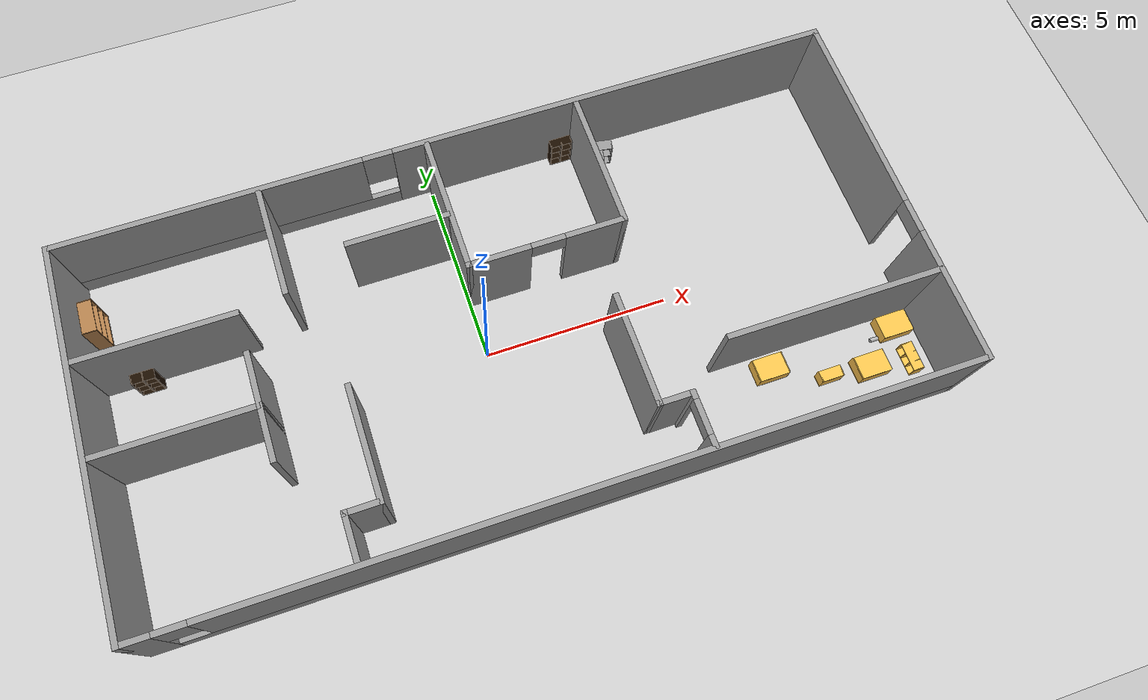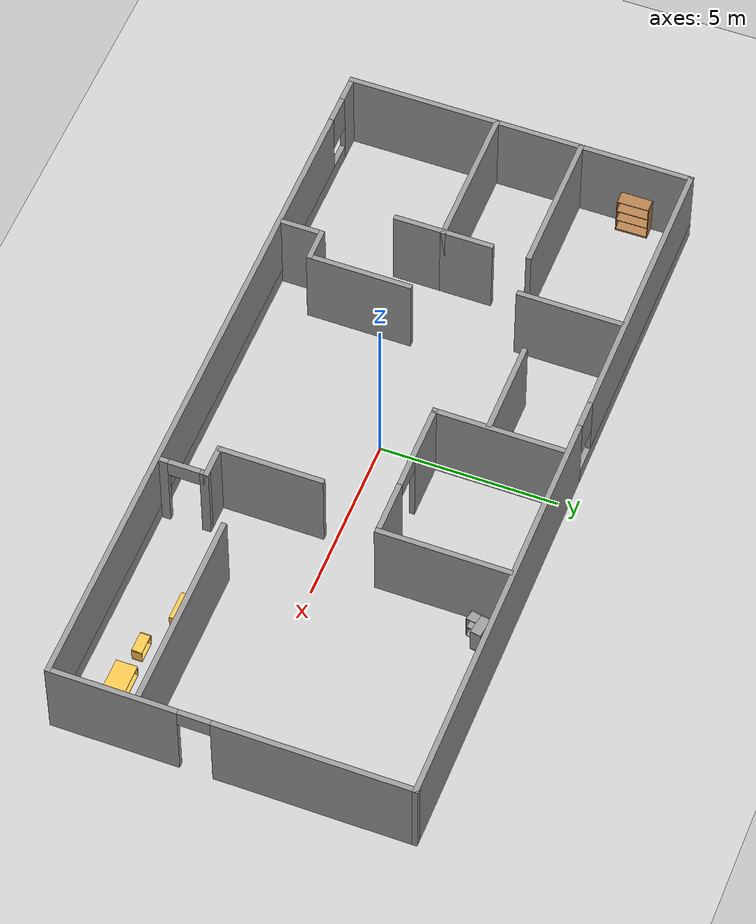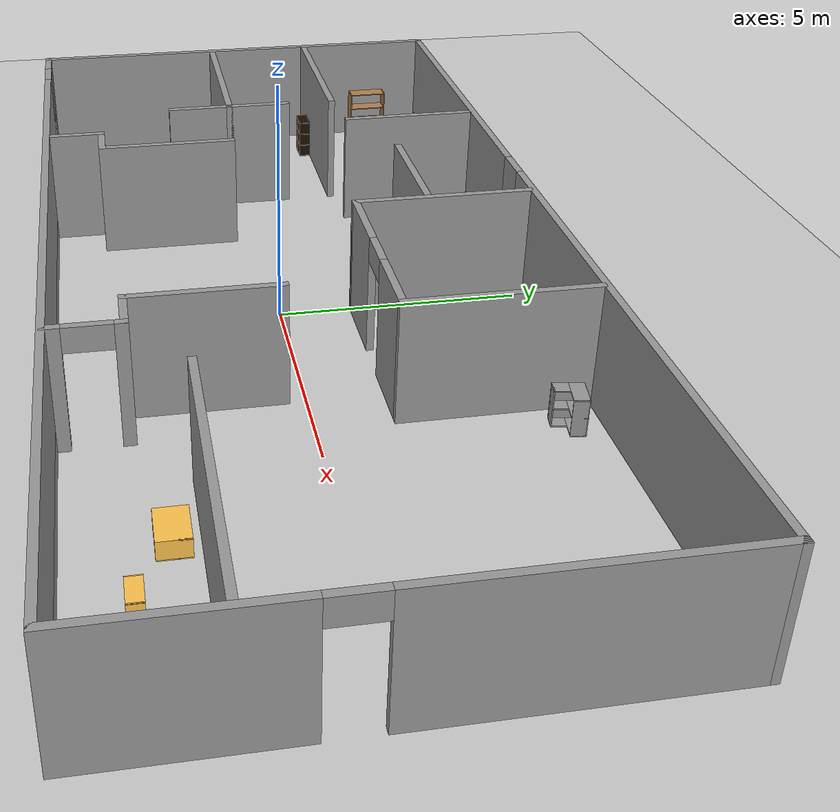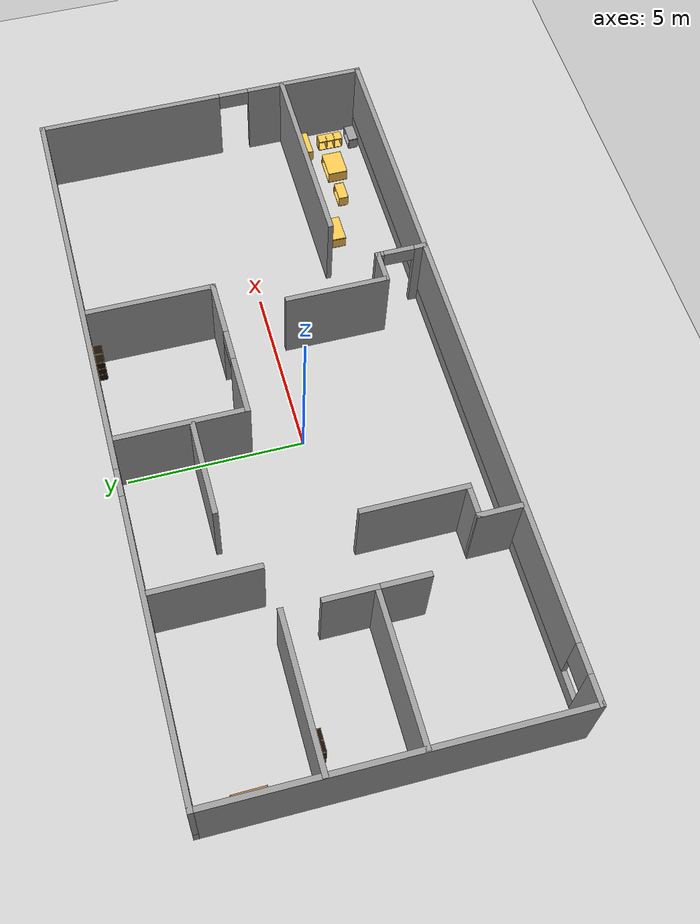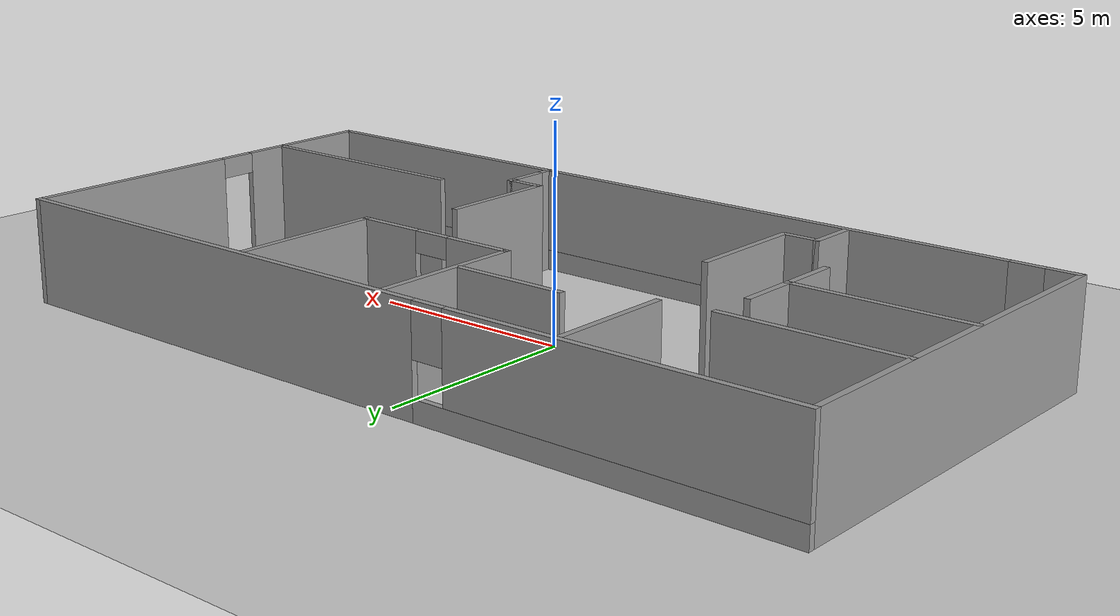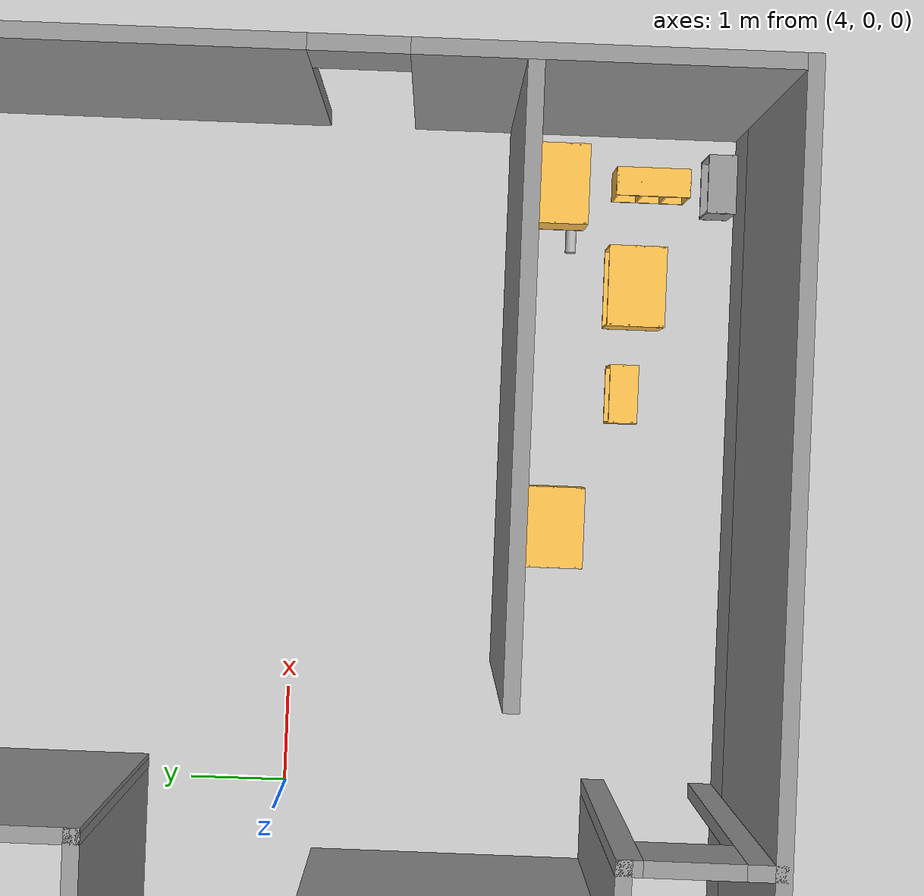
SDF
<sdf version="1.7">
 <world name="default">
  <light name="sun" type="directional">
   <pose>0 0 10 0 -0 0</pose>
   <diffuse>0.8 0.8 0.8 1</diffuse>
   <specular>0.2 0.2 0.2 1</specular>
   <attenuation>
    <range>1000</range>
    <constant>0.9</constant>
    <linear>0.01</linear>
    <quadratic>0.001</quadratic>
   </attenuation>
   <direction>-0.5 0.1 -0.9</direction>
   <spot><inner_angle>0</inner_angle><outer_angle>0</outer_angle><falloff>0</falloff></spot>
  </light>
  <model name="ground_plane">
   <static>1</static>
   <link name="link">
    <collision name="collision">
     <geometry><plane><normal>0 0 1</normal><size>100 100</size></plane></geometry>
     <surface>
      <contact><collide_bitmask>65535</collide_bitmask></contact>
      <friction><ode><mu>100</mu><mu2>50</mu2></ode></friction>
     </surface>
    </collision>
    <visual name="visual">
     <cast_shadows>0</cast_shadows>
     <geometry><plane><normal>0 0 1</normal><size>100 100</size></plane></geometry>
     <material>
      <script><uri>file://media/materials/scripts/gazebo.material</uri><name>Gazebo/Grey</name></script>
     </material>
    </visual>
   </link>
  </model>
  <gravity>0 0 -9.8</gravity>
  <magnetic_field>6e-06 2.3e-05 -4.2e-05</magnetic_field>
  <atmosphere type="adiabatic"/>
  <physics type="ode">
   <max_step_size>0.001</max_step_size>
   <real_time_factor>1</real_time_factor>
   <real_time_update_rate>1000</real_time_update_rate>
  </physics>
  <scene><ambient>0.4 0.4 0.4 1</ambient><background>0.7 0.7 0.7 1</background><shadows>1</shadows></scene>
  <audio><device>default</device></audio>
  <spherical_coordinates>
   <surface_model>EARTH_WGS84</surface_model>
   <latitude_deg>0</latitude_deg>
   <longitude_deg>0</longitude_deg>
   <elevation>0</elevation>
   <heading_deg>0</heading_deg>
  </spherical_coordinates>
  <model name="Untitled">
   <pose>0.655068 0.309447 0 0 -0 0</pose>
   <link name="Wall_1">
    <collision name="Wall_1_Collision">
     <geometry><box><size>10 0.15 2.5</size></box></geometry>
     <pose>0 0 1.25 0 -0 0</pose>
    </collision>
    <visual name="Wall_1_Visual">
     <pose>0 0 1.25 0 -0 0</pose>
     <geometry><box><size>10 0.15 2.5</size></box></geometry>
     <material>
      <script><uri>file://media/materials/scripts/gazebo.material</uri><name>Gazebo/Grey</name></script>
      <ambient>1 1 1 1</ambient>
     </material>
     <meta><layer>0</layer></meta>
    </visual>
    <pose>-10.425 0 0 0 -0 -1.5708</pose>
   </link>
   <link name="Wall_11">
    <collision name="Wall_11_Collision">
     <geometry><box><size>4.25 0.15 2.5</size></box></geometry>
     <pose>0 0 1.25 0 -0 0</pose>
    </collision>
    <visual name="Wall_11_Visual">
     <pose>0 0 1.25 0 -0 0</pose>
     <geometry><box><size>4.25 0.15 2.5</size></box></geometry>
     <material>
      <script><uri>file://media/materials/scripts/gazebo.material</uri><name>Gazebo/Grey</name></script>
      <ambient>1 1 1 1</ambient>
     </material>
     <meta><layer>0</layer></meta>
    </visual>
    <pose>-8.36177 1.77745 0 0 -0 0</pose>
   </link>
   <link name="Wall_13">
    <collision name="Wall_13_Collision">
     <geometry><box><size>4.25 0.15 2.5</size></box></geometry>
     <pose>0 0 1.25 0 -0 0</pose>
    </collision>
    <visual name="Wall_13_Visual">
     <pose>0 0 1.25 0 -0 0</pose>
     <geometry><box><size>4.25 0.15 2.5</size></box></geometry>
     <material>
      <script><uri>file://media/materials/scripts/gazebo.material</uri><name>Gazebo/Grey</name></script>
      <ambient>1 1 1 1</ambient>
     </material>
     <meta><layer>0</layer></meta>
    </visual>
    <pose>-8.34855 -0.669174 0 0 -0 0</pose>
   </link>
   <link name="Wall_14">
    <collision name="Wall_14_Collision">
     <geometry><box><size>1.5 0.15 2.5</size></box></geometry>
     <pose>0 0 1.25 0 -0 0</pose>
    </collision>
    <visual name="Wall_14_Visual">
     <pose>0 0 1.25 0 -0 0</pose>
     <geometry><box><size>1.5 0.15 2.5</size></box></geometry>
     <material>
      <script><uri>file://media/materials/scripts/gazebo.material</uri><name>Gazebo/Grey</name></script>
      <ambient>1 1 1 1</ambient>
     </material>
     <meta><layer>0</layer></meta>
    </visual>
    <pose>-6.29855 0.005825 0 0 -0 1.5708</pose>
   </link>
   <link name="Wall_16">
    <collision name="Wall_16_Collision">
     <geometry><box><size>1.5 0.15 2.5</size></box></geometry>
     <pose>0 0 1.25 0 -0 0</pose>
    </collision>
    <visual name="Wall_16_Visual">
     <pose>0 0 1.25 0 -0 0</pose>
     <geometry><box><size>1.5 0.15 2.5</size></box></geometry>
     <material>
      <script><uri>file://media/materials/scripts/gazebo.material</uri><name>Gazebo/Grey</name></script>
      <ambient>1 1 1 1</ambient>
     </material>
     <meta><layer>0</layer></meta>
    </visual>
    <pose>-6.29855 -1.34417 0 0 -0 -1.5708</pose>
   </link>
   <link name="Wall_18">
    <collision name="Wall_18_Collision">
     <geometry><box><size>1.25 0.15 2.5</size></box></geometry>
     <pose>0 0 1.25 0 -0 0</pose>
    </collision>
    <visual name="Wall_18_Visual">
     <pose>0 0 1.25 0 -0 0</pose>
     <geometry><box><size>1.25 0.15 2.5</size></box></geometry>
     <material>
      <script><uri>file://media/materials/scripts/gazebo.material</uri><name>Gazebo/Grey</name></script>
      <ambient>1 1 1 1</ambient>
     </material>
     <meta><layer>0</layer></meta>
    </visual>
    <pose>-5.06888 -4.2586 0 0 -0 1.5708</pose>
   </link>
   <link name="Wall_19">
    <collision name="Wall_19_Collision">
     <geometry><box><size>1 0.15 2.5</size></box></geometry>
     <pose>0 0 1.25 0 -0 0</pose>
    </collision>
    <visual name="Wall_19_Visual">
     <pose>0 0 1.25 0 -0 0</pose>
     <geometry><box><size>1 0.15 2.5</size></box></geometry>
     <material>
      <script><uri>file://media/materials/scripts/gazebo.material</uri><name>Gazebo/Grey</name></script>
      <ambient>1 1 1 1</ambient>
     </material>
     <meta><layer>0</layer></meta>
    </visual>
    <pose>-4.64388 -3.7086 0 0 -0 0</pose>
   </link>
   <link name="Wall_2">
    <pose>0 -4.925 0 0 -0 0</pose>
    <visual name="Wall_2_Visual_0">
     <pose>-10.0872 0 1.25 0 -0 0</pose>
     <geometry><box><size>0.825575 0.15 2.5</size></box></geometry>
     <material>
      <script><uri>file://media/materials/scripts/gazebo.material</uri><name>Gazebo/Grey</name></script>
      <ambient>1 1 1 1</ambient>
     </material>
     <meta><layer>0</layer></meta>
    </visual>
    <collision name="Wall_2_Collision_0">
     <geometry><box><size>0.825575 0.15 2.5</size></box></geometry>
     <pose>-10.0872 0 1.25 0 -0 0</pose>
    </collision>
    <visual name="Wall_2_Visual_1">
     <pose>0.412787 0 0.25 0 -0 0</pose>
     <geometry><box><size>20.1744 0.15 0.5</size></box></geometry>
     <material>
      <script><uri>file://media/materials/scripts/gazebo.material</uri><name>Gazebo/Grey</name></script>
      <ambient>1 1 1 1</ambient>
     </material>
     <meta><layer>0</layer></meta>
    </visual>
    <collision name="Wall_2_Collision_1">
     <geometry><box><size>20.1744 0.15 0.5</size></box></geometry>
     <pose>0.412787 0 0.25 0 -0 0</pose>
    </collision>
    <visual name="Wall_2_Visual_2">
     <pose>0.812787 0 1.5 0 -0 0</pose>
     <geometry><box><size>19.3744 0.15 2</size></box></geometry>
     <material>
      <script><uri>file://media/materials/scripts/gazebo.material</uri><name>Gazebo/Grey</name></script>
      <ambient>1 1 1 1</ambient>
     </material>
     <meta><layer>0</layer></meta>
    </visual>
    <collision name="Wall_2_Collision_2">
     <geometry><box><size>19.3744 0.15 2</size></box></geometry>
     <pose>0.812787 0 1.5 0 -0 0</pose>
    </collision>
    <visual name="Wall_2_Visual_3">
     <pose>-9.27443 0 1.9 0 -0 0</pose>
     <geometry><box><size>0.8 0.15 1.2</size></box></geometry>
     <material>
      <script><uri>file://media/materials/scripts/gazebo.material</uri><name>Gazebo/Grey</name></script>
      <ambient>1 1 1 1</ambient>
     </material>
     <meta><layer>0</layer></meta>
    </visual>
    <collision name="Wall_2_Collision_3">
     <geometry><box><size>0.8 0.15 1.2</size></box></geometry>
     <pose>-9.27443 0 1.9 0 -0 0</pose>
    </collision>
   </link>
   <link name="Wall_20">
    <collision name="Wall_20_Collision">
     <geometry><box><size>3 0.15 2.5</size></box></geometry>
     <pose>0 0 1.25 0 -0 0</pose>
    </collision>
    <visual name="Wall_20_Visual">
     <pose>0 0 1.25 0 -0 0</pose>
     <geometry><box><size>3 0.15 2.5</size></box></geometry>
     <material>
      <script><uri>file://media/materials/scripts/gazebo.material</uri><name>Gazebo/Grey</name></script>
      <ambient>1 1 1 1</ambient>
     </material>
     <meta><layer>0</layer></meta>
    </visual>
    <pose>-4.21887 -2.2836 0 0 -0 1.5708</pose>
   </link>
   <link name="Wall_25">
    <collision name="Wall_25_Collision">
     <geometry><box><size>2.75 0.15 2.5</size></box></geometry>
     <pose>0 0 1.25 0 -0 0</pose>
    </collision>
    <visual name="Wall_25_Visual">
     <pose>0 0 1.25 0 -0 0</pose>
     <geometry><box><size>2.75 0.15 2.5</size></box></geometry>
     <material>
      <script><uri>file://media/materials/scripts/gazebo.material</uri><name>Gazebo/Grey</name></script>
      <ambient>1 1 1 1</ambient>
     </material>
     <meta><layer>0</layer></meta>
    </visual>
    <pose>-1.99673 2.72965 0 0 -0 0</pose>
   </link>
   <link name="Wall_3">
    <pose>10.425 0 0 0 -0 1.5708</pose>
    <visual name="Wall_3_Visual_0">
     <pose>-3.21168 0 1.25 0 -0 0</pose>
     <geometry><box><size>3.57665 0.15 2.5</size></box></geometry>
     <material>
      <script><uri>file://media/materials/scripts/gazebo.material</uri><name>Gazebo/Grey</name></script>
      <ambient>1 1 1 1</ambient>
     </material>
     <meta><layer>0</layer></meta>
    </visual>
    <collision name="Wall_3_Collision_0">
     <geometry><box><size>3.57665 0.15 2.5</size></box></geometry>
     <pose>-3.21168 0 1.25 0 -0 0</pose>
    </collision>
    <visual name="Wall_3_Visual_1">
     <pose>2.23833 0 1.25 0 -0 0</pose>
     <geometry><box><size>5.52335 0.15 2.5</size></box></geometry>
     <material>
      <script><uri>file://media/materials/scripts/gazebo.material</uri><name>Gazebo/Grey</name></script>
      <ambient>1 1 1 1</ambient>
     </material>
     <meta><layer>0</layer></meta>
    </visual>
    <collision name="Wall_3_Collision_1">
     <geometry><box><size>5.52335 0.15 2.5</size></box></geometry>
     <pose>2.23833 0 1.25 0 -0 0</pose>
    </collision>
    <visual name="Wall_3_Visual_2">
     <pose>-0.97335 0 2.25 0 -0 0</pose>
     <geometry><box><size>0.9 0.15 0.5</size></box></geometry>
     <material>
      <script><uri>file://media/materials/scripts/gazebo.material</uri><name>Gazebo/Grey</name></script>
      <ambient>1 1 1 1</ambient>
     </material>
     <meta><layer>0</layer></meta>
    </visual>
    <collision name="Wall_3_Collision_2">
     <geometry><box><size>0.9 0.15 0.5</size></box></geometry>
     <pose>-0.97335 0 2.25 0 -0 0</pose>
    </collision>
   </link>
   <link name="Wall_4">
    <pose>0 4.925 0 0 -0 3.14159</pose>
    <visual name="Wall_4_Visual_0">
     <pose>-4.49595 0 1.25 0 -0 0</pose>
     <geometry><box><size>12.0081 0.15 2.5</size></box></geometry>
     <material>
      <script><uri>file://media/materials/scripts/gazebo.material</uri><name>Gazebo/Grey</name></script>
      <ambient>1 1 1 1</ambient>
     </material>
     <meta><layer>0</layer></meta>
    </visual>
    <collision name="Wall_4_Collision_0">
     <geometry><box><size>12.0081 0.15 2.5</size></box></geometry>
     <pose>-4.49595 0 1.25 0 -0 0</pose>
    </collision>
    <visual name="Wall_4_Visual_1">
     <pose>6.00405 0 0.25 0 -0 0</pose>
     <geometry><box><size>8.9919 0.15 0.5</size></box></geometry>
     <material>
      <script><uri>file://media/materials/scripts/gazebo.material</uri><name>Gazebo/Grey</name></script>
      <ambient>1 1 1 1</ambient>
     </material>
     <meta><layer>0</layer></meta>
    </visual>
    <collision name="Wall_4_Collision_1">
     <geometry><box><size>8.9919 0.15 0.5</size></box></geometry>
     <pose>6.00405 0 0.25 0 -0 0</pose>
    </collision>
    <visual name="Wall_4_Visual_2">
     <pose>6.40405 0 1.5 0 -0 0</pose>
     <geometry><box><size>8.1919 0.15 2</size></box></geometry>
     <material>
      <script><uri>file://media/materials/scripts/gazebo.material</uri><name>Gazebo/Grey</name></script>
      <ambient>1 1 1 1</ambient>
     </material>
     <meta><layer>0</layer></meta>
    </visual>
    <collision name="Wall_4_Collision_2">
     <geometry><box><size>8.1919 0.15 2</size></box></geometry>
     <pose>6.40405 0 1.5 0 -0 0</pose>
    </collision>
    <visual name="Wall_4_Visual_3">
     <pose>1.9081 0 1.9 0 -0 0</pose>
     <geometry><box><size>0.8 0.15 1.2</size></box></geometry>
     <material>
      <script><uri>file://media/materials/scripts/gazebo.material</uri><name>Gazebo/Grey</name></script>
      <ambient>1 1 1 1</ambient>
     </material>
     <meta><layer>0</layer></meta>
    </visual>
    <collision name="Wall_4_Collision_3">
     <geometry><box><size>0.8 0.15 1.2</size></box></geometry>
     <pose>1.9081 0 1.9 0 -0 0</pose>
    </collision>
   </link>
   <link name="Wall_40">
    <collision name="Wall_40_Collision">
     <geometry><box><size>3 0.15 2.5</size></box></geometry>
     <pose>0 0 1.25 0 -0 0</pose>
    </collision>
    <visual name="Wall_40_Visual">
     <pose>0 0 1.25 0 -0 0</pose>
     <geometry><box><size>3 0.15 2.5</size></box></geometry>
     <material>
      <script><uri>file://media/materials/scripts/gazebo.material</uri><name>Gazebo/Grey</name></script>
      <ambient>1 1 1 1</ambient>
     </material>
     <meta><layer>0</layer></meta>
    </visual>
    <pose>2.56024 -2.11336 0 0 -0 -1.5708</pose>
   </link>
   <link name="Wall_41">
    <collision name="Wall_41_Collision">
     <geometry><box><size>1 0.15 2.5</size></box></geometry>
     <pose>0 0 1.25 0 -0 0</pose>
    </collision>
    <visual name="Wall_41_Visual">
     <pose>0 0 1.25 0 -0 0</pose>
     <geometry><box><size>1 0.15 2.5</size></box></geometry>
     <material>
      <script><uri>file://media/materials/scripts/gazebo.material</uri><name>Gazebo/Grey</name></script>
      <ambient>1 1 1 1</ambient>
     </material>
     <meta><layer>0</layer></meta>
    </visual>
    <pose>2.98524 -3.53836 0 0 -0 0</pose>
   </link>
   <link name="Wall_42">
    <pose>3.41024 -4.21336 0 0 -0 -1.5708</pose>
    <visual name="Wall_42_Visual_0">
     <pose>-0.628703 0 1.25 0 -0 0</pose>
     <geometry><box><size>0.242595 0.15 2.5</size></box></geometry>
     <material>
      <script><uri>file://media/materials/scripts/gazebo.material</uri><name>Gazebo/Grey</name></script>
      <ambient>1 1 1 1</ambient>
     </material>
     <meta><layer>0</layer></meta>
    </visual>
    <collision name="Wall_42_Collision_0">
     <geometry><box><size>0.242595 0.15 2.5</size></box></geometry>
     <pose>-0.628703 0 1.25 0 -0 0</pose>
    </collision>
    <visual name="Wall_42_Visual_1">
     <pose>0.571297 0 1.25 0 -0 0</pose>
     <geometry><box><size>0.357405 0.15 2.5</size></box></geometry>
     <material>
      <script><uri>file://media/materials/scripts/gazebo.material</uri><name>Gazebo/Grey</name></script>
      <ambient>1 1 1 1</ambient>
     </material>
     <meta><layer>0</layer></meta>
    </visual>
    <collision name="Wall_42_Collision_1">
     <geometry><box><size>0.357405 0.15 2.5</size></box></geometry>
     <pose>0.571297 0 1.25 0 -0 0</pose>
    </collision>
    <visual name="Wall_42_Visual_2">
     <pose>-0.057405 0 2.25 0 -0 0</pose>
     <geometry><box><size>0.9 0.15 0.5</size></box></geometry>
     <material>
      <script><uri>file://media/materials/scripts/gazebo.material</uri><name>Gazebo/Grey</name></script>
      <ambient>1 1 1 1</ambient>
     </material>
     <meta><layer>0</layer></meta>
    </visual>
    <collision name="Wall_42_Collision_2">
     <geometry><box><size>0.9 0.15 0.5</size></box></geometry>
     <pose>-0.057405 0 2.25 0 -0 0</pose>
    </collision>
   </link>
   <link name="Wall_45">
    <collision name="Wall_45_Collision">
     <geometry><box><size>5.75 0.15 2.5</size></box></geometry>
     <pose>0 0 1.25 0 -0 0</pose>
    </collision>
    <visual name="Wall_45_Visual">
     <pose>0 0 1.25 0 -0 0</pose>
     <geometry><box><size>5.75 0.15 2.5</size></box></geometry>
     <material>
      <script><uri>file://media/materials/scripts/gazebo.material</uri><name>Gazebo/Grey</name></script>
      <ambient>1 1 1 1</ambient>
     </material>
     <meta><layer>0</layer></meta>
    </visual>
    <pose>7.57753 -2.51341 0 0 -0 3.14159</pose>
   </link>
   <link name="Wall_47">
    <collision name="Wall_47_Collision">
     <geometry><box><size>3.75 0.15 2.5</size></box></geometry>
     <pose>0 0 1.25 0 -0 0</pose>
    </collision>
    <visual name="Wall_47_Visual">
     <pose>0 0 1.25 0 -0 0</pose>
     <geometry><box><size>3.75 0.15 2.5</size></box></geometry>
     <material>
      <script><uri>file://media/materials/scripts/gazebo.material</uri><name>Gazebo/Grey</name></script>
      <ambient>1 1 1 1</ambient>
     </material>
     <meta><layer>0</layer></meta>
    </visual>
    <pose>-0.603184 3.03241 0 0 -0 -1.5708</pose>
   </link>
   <link name="Wall_48">
    <pose>1.44682 1.23241 0 0 -0 0</pose>
    <visual name="Wall_48_Visual_0">
     <pose>-1.2707 0 1.25 0 -0 0</pose>
     <geometry><box><size>1.7086 0.15 2.5</size></box></geometry>
     <material>
      <script><uri>file://media/materials/scripts/gazebo.material</uri><name>Gazebo/Grey</name></script>
      <ambient>1 1 1 1</ambient>
     </material>
     <meta><layer>0</layer></meta>
    </visual>
    <collision name="Wall_48_Collision_0">
     <geometry><box><size>1.7086 0.15 2.5</size></box></geometry>
     <pose>-1.2707 0 1.25 0 -0 0</pose>
    </collision>
    <visual name="Wall_48_Visual_1">
     <pose>1.3043 0 1.25 0 -0 0</pose>
     <geometry><box><size>1.6414 0.15 2.5</size></box></geometry>
     <material>
      <script><uri>file://media/materials/scripts/gazebo.material</uri><name>Gazebo/Grey</name></script>
      <ambient>1 1 1 1</ambient>
     </material>
     <meta><layer>0</layer></meta>
    </visual>
    <collision name="Wall_48_Collision_1">
     <geometry><box><size>1.6414 0.15 2.5</size></box></geometry>
     <pose>1.3043 0 1.25 0 -0 0</pose>
    </collision>
    <visual name="Wall_48_Visual_2">
     <pose>0.033599 0 2.25 0 -0 0</pose>
     <geometry><box><size>0.9 0.15 0.5</size></box></geometry>
     <material>
      <script><uri>file://media/materials/scripts/gazebo.material</uri><name>Gazebo/Grey</name></script>
      <ambient>1 1 1 1</ambient>
     </material>
     <meta><layer>0</layer></meta>
    </visual>
    <collision name="Wall_48_Collision_2">
     <geometry><box><size>0.9 0.15 0.5</size></box></geometry>
     <pose>0.033599 0 2.25 0 -0 0</pose>
    </collision>
   </link>
   <link name="Wall_49">
    <collision name="Wall_49_Collision">
     <geometry><box><size>3.75 0.15 2.5</size></box></geometry>
     <pose>0 0 1.25 0 -0 0</pose>
    </collision>
    <visual name="Wall_49_Visual">
     <pose>0 0 1.25 0 -0 0</pose>
     <geometry><box><size>3.75 0.15 2.5</size></box></geometry>
     <material>
      <script><uri>file://media/materials/scripts/gazebo.material</uri><name>Gazebo/Grey</name></script>
      <ambient>1 1 1 1</ambient>
     </material>
     <meta><layer>0</layer></meta>
    </visual>
    <pose>3.49682 3.03241 0 0 -0 1.5708</pose>
   </link>
   <link name="Wall_7">
    <collision name="Wall_7_Collision">
     <geometry><box><size>3 0.15 2.5</size></box></geometry>
     <pose>0 0 1.25 0 -0 0</pose>
    </collision>
    <visual name="Wall_7_Visual">
     <pose>0 0 1.25 0 -0 0</pose>
     <geometry><box><size>3 0.15 2.5</size></box></geometry>
     <material>
      <script><uri>file://media/materials/scripts/gazebo.material</uri><name>Gazebo/Grey</name></script>
      <ambient>1 1 1 1</ambient>
     </material>
     <meta><layer>0</layer></meta>
    </visual>
    <pose>-5.05565 3.38097 0 0 -0 -1.5708</pose>
   </link>
   <static>1</static>
  </model>
  <model name="bookshelf">
   <static>1</static>
   <link name="link">
    <inertial><mass>1</mass></inertial>
    <collision name="back">
     <pose>0 0.005 0.6 0 -0 0</pose>
     <geometry><box><size>0.9 0.01 1.2</size></box></geometry>
    </collision>
    <visual name="visual1">
     <pose>0 0.005 0.6 0 -0 0</pose>
     <geometry><box><size>0.9 0.01 1.2</size></box></geometry>
     <material>
      <script><uri>file://media/materials/scripts/gazebo.material</uri><name>Gazebo/Wood</name></script>
     </material>
    </visual>
    <collision name="left_side">
     <pose>0.45 -0.195 0.6 0 -0 0</pose>
     <geometry><box><size>0.02 0.4 1.2</size></box></geometry>
    </collision>
    <visual name="visual2">
     <pose>0.45 -0.195 0.6 0 -0 0</pose>
     <geometry><box><size>0.02 0.4 1.2</size></box></geometry>
     <material>
      <script><uri>file://media/materials/scripts/gazebo.material</uri><name>Gazebo/Wood</name></script>
     </material>
    </visual>
    <collision name="right_side">
     <pose>-0.45 -0.195 0.6 0 -0 0</pose>
     <geometry><box><size>0.02 0.4 1.2</size></box></geometry>
    </collision>
    <visual name="visual3">
     <pose>-0.45 -0.195 0.6 0 -0 0</pose>
     <geometry><box><size>0.02 0.4 1.2</size></box></geometry>
     <material>
      <script><uri>file://media/materials/scripts/gazebo.material</uri><name>Gazebo/Wood</name></script>
     </material>
    </visual>
    <collision name="bottom">
     <pose>0 -0.195 0.03 0 -0 0</pose>
     <geometry><box><size>0.88 0.4 0.06</size></box></geometry>
    </collision>
    <visual name="visual4">
     <pose>0 -0.195 0.03 0 -0 0</pose>
     <geometry><box><size>0.88 0.4 0.06</size></box></geometry>
     <material>
      <script><uri>file://media/materials/scripts/gazebo.material</uri><name>Gazebo/Wood</name></script>
     </material>
    </visual>
    <collision name="top">
     <pose>0 -0.195 1.19 0 -0 0</pose>
     <geometry><box><size>0.88 0.4 0.02</size></box></geometry>
    </collision>
    <visual name="visual5">
     <pose>0 -0.195 1.19 0 -0 0</pose>
     <geometry><box><size>0.88 0.4 0.02</size></box></geometry>
     <material>
      <script><uri>file://media/materials/scripts/gazebo.material</uri><name>Gazebo/Wood</name></script>
     </material>
    </visual>
    <collision name="low_shelf">
     <pose>0 -0.195 0.43 0 -0 0</pose>
     <geometry><box><size>0.88 0.4 0.02</size></box></geometry>
    </collision>
    <visual name="visual6">
     <pose>0 -0.195 0.43 0 -0 0</pose>
     <geometry><box><size>0.88 0.4 0.02</size></box></geometry>
     <material>
      <script><uri>file://media/materials/scripts/gazebo.material</uri><name>Gazebo/Wood</name></script>
     </material>
    </visual>
    <collision name="high_shelf">
     <pose>0 -0.195 0.8 0 -0 0</pose>
     <geometry><box><size>0.88 0.4 0.02</size></box></geometry>
    </collision>
    <visual name="visual7">
     <pose>0 -0.195 0.8 0 -0 0</pose>
     <geometry><box><size>0.88 0.4 0.02</size></box></geometry>
     <material>
      <script><uri>file://media/materials/scripts/gazebo.material</uri><name>Gazebo/Wood</name></script>
     </material>
    </visual>
   </link>
   <pose>-9.7163 3.79112 0 0 -0 1.58343</pose>
  </model>
  <model name="beer">
   <link name="link">
    <pose>0 0 0.115 0 -0 0</pose>
    <inertial>
     <mass>0.39</mass>
     <inertia><ixx>0.00058</ixx><ixy>0</ixy><ixz>0</ixz><iyy>0.00058</iyy><iyz>0</iyz><izz>0.00019</izz></inertia>
    </inertial>
    <collision name="collision">
     <geometry><cylinder><radius>0.055</radius><length>0.23</length></cylinder></geometry>
    </collision>
    <visual name="visual">
     <geometry><cylinder><radius>0.055</radius><length>0.23</length></cylinder></geometry>
     <material>
      <script>
       <uri>model://beer/materials/scripts</uri>
       <uri>model://beer/materials/textures</uri>
       <name>Beer/Diffuse</name>
      </script>
     </material>
    </visual>
   </link>
   <pose>9.74094 -2.80996 0.054918 1.56964 1.25964 1.56969</pose>
  </model>
  <model name="6_Cube_StorageE">
   <link name="Wall_0">
    <pose>0 0 0.01 0 -0 0</pose>
    <inertial>
     <mass>1.6201</mass>
     <inertia><ixx>0.0119</ixx><iyy>0.0631</iyy><izz>0.0513</izz><ixy>0</ixy><ixz>0</ixz><iyz>0</iyz></inertia>
    </inertial>
    <collision name="Wall_0_Collision"><geometry><box><size>0.616 0.296 0.02</size></box></geometry></collision>
    <visual name="Wall_0_Visual">
     <geometry><box><size>0.616 0.296 0.02</size></box></geometry>
     <material>
      <script><uri>file://media/materials/scripts/gazebo.material</uri><name>Gazebo/Grey</name></script>
      <ambient>0.105882 0.0509804 0 1</ambient>
     </material>
    </visual>
   </link>
   <joint name="0_2" type="fixed">
    <pose>-0.308 0 0 0 -0 0</pose>
    <parent>Wall_2</parent>
    <child>Wall_0</child>
    <axis><xyz>1 0 0</xyz><limit><lower>-1e+16</lower><upper>1e+16</upper></limit></axis>
   </joint>
   <joint name="0_12" type="fixed">
    <parent>Wall_12</parent>
    <child>Wall_0</child>
    <axis><xyz>0 0 1</xyz><limit><lower>-1e+16</lower><upper>1e+16</upper></limit></axis>
   </joint>
   <joint name="0_4" type="fixed">
    <pose>0.308 0 0 0 -0 0</pose>
    <parent>Wall_4</parent>
    <child>Wall_0</child>
    <axis><xyz>1 0 0</xyz><limit><lower>-1e+16</lower><upper>1e+16</upper></limit></axis>
   </joint>
   <link name="Wall_10">
    <pose>0 0 0.61 0 -0 0</pose>
    <inertial>
     <mass>1.6201</mass>
     <inertia><ixx>0.0119</ixx><iyy>0.0631</iyy><izz>0.0513</izz><ixy>0</ixy><ixz>0</ixz><iyz>0</iyz></inertia>
    </inertial>
    <collision name="Wall_10_Collision"><geometry><box><size>0.616 0.296 0.02</size></box></geometry></collision>
    <visual name="Wall_10_Visual">
     <geometry><box><size>0.616 0.296 0.02</size></box></geometry>
     <material>
      <script><uri>file://media/materials/scripts/gazebo.material</uri><name>Gazebo/Grey</name></script>
      <ambient>0.105882 0.0509804 0 1</ambient>
     </material>
    </visual>
   </link>
   <joint name="10_2" type="fixed">
    <pose>-0.308 0 0 0 -0 0</pose>
    <parent>Wall_2</parent>
    <child>Wall_10</child>
    <axis><xyz>1 0 0</xyz><limit><lower>-1e+16</lower><upper>1e+16</upper></limit></axis>
   </joint>
   <joint name="10_12" type="fixed">
    <parent>Wall_12</parent>
    <child>Wall_10</child>
    <axis><xyz>0 0 1</xyz><limit><lower>-1e+16</lower><upper>1e+16</upper></limit></axis>
   </joint>
   <joint name="10_4" type="fixed">
    <pose>0.308 0 0 0 -0 0</pose>
    <parent>Wall_4</parent>
    <child>Wall_10</child>
    <axis><xyz>1 0 0</xyz><limit><lower>-1e+16</lower><upper>1e+16</upper></limit></axis>
   </joint>
   <link name="Wall_12">
    <pose>0 0 0.4575 0 -0 0</pose>
    <inertial>
     <mass>2.4065</mass>
     <inertia><ixx>0.0177</ixx><iyy>0.1855</iyy><izz>0.168</izz><ixy>0</ixy><ixz>0</ixz><iyz>0</iyz></inertia>
    </inertial>
    <collision name="Wall_12_Collision"><geometry><box><size>0.02 0.296 0.915</size></box></geometry></collision>
    <visual name="Wall_12_Visual">
     <geometry><box><size>0.02 0.296 0.915</size></box></geometry>
     <material>
      <script><uri>file://media/materials/scripts/gazebo.material</uri><name>Gazebo/Grey</name></script>
      <ambient>0.105882 0.0509804 0 1</ambient>
     </material>
    </visual>
   </link>
   <link name="Wall_2">
    <pose>-0.298 0 0.4575 0 -0 0</pose>
    <inertial>
     <mass>2.4065</mass>
     <inertia><ixx>0.0177</ixx><iyy>0.1855</iyy><izz>0.168</izz><ixy>0</ixy><ixz>0</ixz><iyz>0</iyz></inertia>
    </inertial>
    <collision name="Wall_2_Collision"><geometry><box><size>0.02 0.296 0.915</size></box></geometry></collision>
    <visual name="Wall_2_Visual">
     <geometry><box><size>0.02 0.296 0.915</size></box></geometry>
     <material>
      <script><uri>file://media/materials/scripts/gazebo.material</uri><name>Gazebo/Grey</name></script>
      <ambient>0.105882 0.0509804 0 1</ambient>
     </material>
    </visual>
   </link>
   <link name="Wall_4">
    <pose>0.298 0 0.4575 0 -0 0</pose>
    <inertial>
     <mass>2.4065</mass>
     <inertia><ixx>0.0177</ixx><iyy>0.1855</iyy><izz>0.168</izz><ixy>0</ixy><ixz>0</ixz><iyz>0</iyz></inertia>
    </inertial>
    <collision name="Wall_4_Collision"><geometry><box><size>0.02 0.296 0.915</size></box></geometry></collision>
    <visual name="Wall_4_Visual">
     <geometry><box><size>0.02 0.296 0.915</size></box></geometry>
     <material>
      <script><uri>file://media/materials/scripts/gazebo.material</uri><name>Gazebo/Grey</name></script>
      <ambient>0.105882 0.0509804 0 1</ambient>
     </material>
    </visual>
   </link>
   <link name="Wall_6">
    <pose>0 0 0.905 0 -0 0</pose>
    <inertial>
     <mass>1.6201</mass>
     <inertia><ixx>0.0119</ixx><iyy>0.0631</iyy><izz>0.0513</izz><ixy>0</ixy><ixz>0</ixz><iyz>0</iyz></inertia>
    </inertial>
    <collision name="Wall_6_Collision"><geometry><box><size>0.616 0.296 0.02</size></box></geometry></collision>
    <visual name="Wall_6_Visual">
     <geometry><box><size>0.616 0.296 0.02</size></box></geometry>
     <material>
      <script><uri>file://media/materials/scripts/gazebo.material</uri><name>Gazebo/Grey</name></script>
      <ambient>0.105882 0.0509804 0 1</ambient>
     </material>
    </visual>
   </link>
   <joint name="6_2" type="fixed">
    <pose>-0.308 0 0 0 -0 0</pose>
    <parent>Wall_2</parent>
    <child>Wall_6</child>
    <axis><xyz>2 0 0</xyz><limit><lower>-1e+16</lower><upper>1e+16</upper></limit></axis>
   </joint>
   <joint name="6_12" type="fixed">
    <parent>Wall_12</parent>
    <child>Wall_6</child>
    <axis><xyz>0 0 1</xyz><limit><lower>-1e+16</lower><upper>1e+16</upper></limit></axis>
   </joint>
   <joint name="6_4" type="fixed">
    <pose>0.308 0 0 0 -0 0</pose>
    <parent>Wall_4</parent>
    <child>Wall_6</child>
    <axis><xyz>1 0 0</xyz><limit><lower>-1e+16</lower><upper>1e+16</upper></limit></axis>
   </joint>
   <link name="Wall_8">
    <pose>0 0 0.305 0 -0 0</pose>
    <inertial>
     <mass>1.6201</mass>
     <inertia><ixx>0.0119</ixx><iyy>0.0631</iyy><izz>0.0513</izz><ixy>0</ixy><ixz>0</ixz><iyz>0</iyz></inertia>
    </inertial>
    <collision name="Wall_8_Collision"><geometry><box><size>0.616 0.296 0.02</size></box></geometry></collision>
    <visual name="Wall_8_Visual">
     <geometry><box><size>0.616 0.296 0.02</size></box></geometry>
     <material>
      <script><uri>file://media/materials/scripts/gazebo.material</uri><name>Gazebo/Grey</name></script>
      <ambient>0.105882 0.0509804 0 1</ambient>
     </material>
    </visual>
   </link>
   <joint name="8_2" type="fixed">
    <pose>-0.308 0 0 0 -0 0</pose>
    <parent>Wall_2</parent>
    <child>Wall_8</child>
    <axis><xyz>1 0 0</xyz><limit><lower>-1e+16</lower><upper>1e+16</upper></limit></axis>
   </joint>
   <joint name="8_12" type="fixed">
    <parent>Wall_12</parent>
    <child>Wall_8</child>
    <axis><xyz>0 0 1</xyz><limit><lower>-1e+16</lower><upper>1e+16</upper></limit></axis>
   </joint>
   <joint name="8_4" type="fixed">
    <pose>0.308 0 0 0 -0 0</pose>
    <parent>Wall_4</parent>
    <child>Wall_8</child>
    <axis><xyz>1 0 0</xyz><limit><lower>-1e+16</lower><upper>1e+16</upper></limit></axis>
   </joint>
   <static>1</static>
   <pose>-8.52802 1.89454 0 0 -0 0</pose>
  </model>
  <model name="Fridge_Cabinet_33x15">
   <link name="Wall_17">
    <pose>0 0 0.01 0 -0 0</pose>
    <inertial>
     <mass>4.8627</mass>
     <inertia><ixx>0.146</ixx><iyy>0.4318</iyy><izz>0.2861</izz><ixy>0</ixy><ixz>0</ixz><iyz>0</iyz></inertia>
    </inertial>
    <collision name="Wall_17_Collision"><geometry><box><size>0.84 0.6 0.02</size></box></geometry></collision>
    <visual name="Wall_17_Visual">
     <geometry><box><size>0.84 0.6 0.02</size></box></geometry>
     <material>
      <script><uri>file://media/materials/scripts/gazebo.material</uri><name>Gazebo/Grey</name></script>
      <ambient>1 0.764706 0.305882 1</ambient>
     </material>
    </visual>
   </link>
   <joint name="17_21" type="fixed">
    <pose>0.42 0 0 0 -0 0</pose>
    <parent>Wall_21</parent>
    <child>Wall_17</child>
    <axis><xyz>1 0 0</xyz><limit><lower>-1e+16</lower><upper>1e+16</upper></limit></axis>
   </joint>
   <joint name="17_19" type="fixed">
    <pose>-0.42 0 0 0 -0 0</pose>
    <parent>Wall_19</parent>
    <child>Wall_17</child>
    <axis><xyz>1 0 0</xyz><limit><lower>-1e+16</lower><upper>1e+16</upper></limit></axis>
   </joint>
   <joint name="17_25" type="fixed">
    <pose>0 -0.3 0 0 -0 0</pose>
    <parent>Wall_25</parent>
    <child>Wall_17</child>
    <axis><xyz>0 1 0</xyz><limit><lower>-1e+16</lower><upper>1e+16</upper></limit></axis>
   </joint>
   <link name="Wall_19">
    <pose>-0.41 0 0.192 0 -0 0</pose>
    <inertial>
     <mass>2.223</mass>
     <inertia><ixx>0.0668</ixx><iyy>0.094</iyy><izz>0.0274</izz><ixy>0</ixy><ixz>0</ixz><iyz>0</iyz></inertia>
    </inertial>
    <collision name="Wall_19_Collision"><geometry><box><size>0.02 0.6 0.384</size></box></geometry></collision>
    <visual name="Wall_19_Visual">
     <geometry><box><size>0.02 0.6 0.384</size></box></geometry>
     <material>
      <script><uri>file://media/materials/scripts/gazebo.material</uri><name>Gazebo/Grey</name></script>
      <ambient>1 0.764706 0.305882 1</ambient>
     </material>
    </visual>
   </link>
   <link name="Wall_21">
    <pose>0.41 0 0.192 0 -0 0</pose>
    <inertial>
     <mass>2.223</mass>
     <inertia><ixx>0.0668</ixx><iyy>0.094</iyy><izz>0.0274</izz><ixy>0</ixy><ixz>0</ixz><iyz>0</iyz></inertia>
    </inertial>
    <collision name="Wall_21_Collision"><geometry><box><size>0.02 0.6 0.384</size></box></geometry></collision>
    <visual name="Wall_21_Visual">
     <geometry><box><size>0.02 0.6 0.384</size></box></geometry>
     <material>
      <script><uri>file://media/materials/scripts/gazebo.material</uri><name>Gazebo/Grey</name></script>
      <ambient>1 0.764706 0.305882 1</ambient>
     </material>
    </visual>
   </link>
   <link name="Wall_23">
    <pose>0 0 0.374 0 -0 0</pose>
    <inertial>
     <mass>4.8627</mass>
     <inertia><ixx>0.146</ixx><iyy>0.4318</iyy><izz>0.2861</izz><ixy>0</ixy><ixz>0</ixz><iyz>0</iyz></inertia>
    </inertial>
    <collision name="Wall_23_Collision"><geometry><box><size>0.84 0.6 0.02</size></box></geometry></collision>
    <visual name="Wall_23_Visual">
     <geometry><box><size>0.84 0.6 0.02</size></box></geometry>
     <material>
      <script><uri>file://media/materials/scripts/gazebo.material</uri><name>Gazebo/Grey</name></script>
      <ambient>1 0.764706 0.305882 1</ambient>
     </material>
    </visual>
   </link>
   <joint name="23_21" type="fixed">
    <pose>0.42 0 0 0 -0 0</pose>
    <parent>Wall_21</parent>
    <child>Wall_23</child>
    <axis><xyz>0 0 1</xyz><limit><lower>-1e+16</lower><upper>1e+16</upper></limit></axis>
   </joint>
   <joint name="23_19" type="fixed">
    <pose>-0.42 0 0 0 -0 0</pose>
    <parent>Wall_19</parent>
    <child>Wall_23</child>
    <axis><xyz>0 0 1</xyz><limit><lower>-1e+16</lower><upper>1e+16</upper></limit></axis>
   </joint>
   <joint name="23_25" type="fixed">
    <pose>0 -0.3 0 0 -0 0</pose>
    <parent>Wall_25</parent>
    <child>Wall_23</child>
    <axis><xyz>0 0 1</xyz><limit><lower>-1e+16</lower><upper>1e+16</upper></limit></axis>
   </joint>
   <link name="Wall_25">
    <pose>0 -0.29 0.19 0 -0 0</pose>
    <inertial>
     <mass>3.0651</mass>
     <inertia><ixx>0.037</ixx><iyy>0.1786</iyy><izz>0.2154</izz><ixy>0</ixy><ixz>0</ixz><iyz>0</iyz></inertia>
    </inertial>
    <collision name="Wall_25_Collision"><geometry><box><size>0.836 0.02 0.38</size></box></geometry></collision>
    <visual name="Wall_25_Visual">
     <geometry><box><size>0.836 0.02 0.38</size></box></geometry>
     <material>
      <script><uri>file://media/materials/scripts/gazebo.material</uri><name>Gazebo/Grey</name></script>
      <ambient>1 0.764706 0.305882 1</ambient>
     </material>
    </visual>
   </link>
   <joint name="25_21" type="fixed">
    <pose>0.42 0 0 0 -0 0</pose>
    <parent>Wall_21</parent>
    <child>Wall_25</child>
    <axis><xyz>0 1 0</xyz><limit><lower>-1e+16</lower><upper>1e+16</upper></limit></axis>
   </joint>
   <joint name="25_19" type="fixed">
    <pose>-0.42 0 0 0 -0 0</pose>
    <parent>Wall_19</parent>
    <child>Wall_25</child>
    <axis><xyz>0 1 0</xyz><limit><lower>-1e+16</lower><upper>1e+16</upper></limit></axis>
   </joint>
   <static>1</static>
   <pose>10.4095 -2.65103 0 0 -0 0</pose>
  </model>
  <model name="Fridge_Cabinet_33x15_0">
   <link name="Wall_17">
    <pose>0 0 0.01 0 -0 0</pose>
    <inertial>
     <mass>4.8627</mass>
     <inertia><ixx>0.146</ixx><iyy>0.4318</iyy><izz>0.2861</izz><ixy>0</ixy><ixz>0</ixz><iyz>0</iyz></inertia>
    </inertial>
    <collision name="Wall_17_Collision"><geometry><box><size>0.84 0.6 0.02</size></box></geometry></collision>
    <visual name="Wall_17_Visual">
     <geometry><box><size>0.84 0.6 0.02</size></box></geometry>
     <material>
      <script><uri>file://media/materials/scripts/gazebo.material</uri><name>Gazebo/Grey</name></script>
      <ambient>1 0.764706 0.305882 1</ambient>
     </material>
    </visual>
   </link>
   <joint name="17_21" type="fixed">
    <pose>0.42 0 0 0 -0 0</pose>
    <parent>Wall_21</parent>
    <child>Wall_17</child>
    <axis><xyz>1 0 0</xyz><limit><lower>-1e+16</lower><upper>1e+16</upper></limit></axis>
   </joint>
   <joint name="17_19" type="fixed">
    <pose>-0.42 0 0 0 -0 0</pose>
    <parent>Wall_19</parent>
    <child>Wall_17</child>
    <axis><xyz>1 0 0</xyz><limit><lower>-1e+16</lower><upper>1e+16</upper></limit></axis>
   </joint>
   <joint name="17_25" type="fixed">
    <pose>0 -0.3 0 0 -0 0</pose>
    <parent>Wall_25</parent>
    <child>Wall_17</child>
    <axis><xyz>0 1 0</xyz><limit><lower>-1e+16</lower><upper>1e+16</upper></limit></axis>
   </joint>
   <link name="Wall_19">
    <pose>-0.41 0 0.192 0 -0 0</pose>
    <inertial>
     <mass>2.223</mass>
     <inertia><ixx>0.0668</ixx><iyy>0.094</iyy><izz>0.0274</izz><ixy>0</ixy><ixz>0</ixz><iyz>0</iyz></inertia>
    </inertial>
    <collision name="Wall_19_Collision"><geometry><box><size>0.02 0.6 0.384</size></box></geometry></collision>
    <visual name="Wall_19_Visual">
     <geometry><box><size>0.02 0.6 0.384</size></box></geometry>
     <material>
      <script><uri>file://media/materials/scripts/gazebo.material</uri><name>Gazebo/Grey</name></script>
      <ambient>1 0.764706 0.305882 1</ambient>
     </material>
    </visual>
   </link>
   <link name="Wall_21">
    <pose>0.41 0 0.192 0 -0 0</pose>
    <inertial>
     <mass>2.223</mass>
     <inertia><ixx>0.0668</ixx><iyy>0.094</iyy><izz>0.0274</izz><ixy>0</ixy><ixz>0</ixz><iyz>0</iyz></inertia>
    </inertial>
    <collision name="Wall_21_Collision"><geometry><box><size>0.02 0.6 0.384</size></box></geometry></collision>
    <visual name="Wall_21_Visual">
     <geometry><box><size>0.02 0.6 0.384</size></box></geometry>
     <material>
      <script><uri>file://media/materials/scripts/gazebo.material</uri><name>Gazebo/Grey</name></script>
      <ambient>1 0.764706 0.305882 1</ambient>
     </material>
    </visual>
   </link>
   <link name="Wall_23">
    <pose>0 0 0.374 0 -0 0</pose>
    <inertial>
     <mass>4.8627</mass>
     <inertia><ixx>0.146</ixx><iyy>0.4318</iyy><izz>0.2861</izz><ixy>0</ixy><ixz>0</ixz><iyz>0</iyz></inertia>
    </inertial>
    <collision name="Wall_23_Collision"><geometry><box><size>0.84 0.6 0.02</size></box></geometry></collision>
    <visual name="Wall_23_Visual">
     <geometry><box><size>0.84 0.6 0.02</size></box></geometry>
     <material>
      <script><uri>file://media/materials/scripts/gazebo.material</uri><name>Gazebo/Grey</name></script>
      <ambient>1 0.764706 0.305882 1</ambient>
     </material>
    </visual>
   </link>
   <joint name="23_21" type="fixed">
    <pose>0.42 0 0 0 -0 0</pose>
    <parent>Wall_21</parent>
    <child>Wall_23</child>
    <axis><xyz>0 0 1</xyz><limit><lower>-1e+16</lower><upper>1e+16</upper></limit></axis>
   </joint>
   <joint name="23_19" type="fixed">
    <pose>-0.42 0 0 0 -0 0</pose>
    <parent>Wall_19</parent>
    <child>Wall_23</child>
    <axis><xyz>0 0 1</xyz><limit><lower>-1e+16</lower><upper>1e+16</upper></limit></axis>
   </joint>
   <joint name="23_25" type="fixed">
    <pose>0 -0.3 0 0 -0 0</pose>
    <parent>Wall_25</parent>
    <child>Wall_23</child>
    <axis><xyz>0 0 1</xyz><limit><lower>-1e+16</lower><upper>1e+16</upper></limit></axis>
   </joint>
   <link name="Wall_25">
    <pose>0 -0.29 0.19 0 -0 0</pose>
    <inertial>
     <mass>3.0651</mass>
     <inertia><ixx>0.037</ixx><iyy>0.1786</iyy><izz>0.2154</izz><ixy>0</ixy><ixz>0</ixz><iyz>0</iyz></inertia>
    </inertial>
    <collision name="Wall_25_Collision"><geometry><box><size>0.836 0.02 0.38</size></box></geometry></collision>
    <visual name="Wall_25_Visual">
     <geometry><box><size>0.836 0.02 0.38</size></box></geometry>
     <material>
      <script><uri>file://media/materials/scripts/gazebo.material</uri><name>Gazebo/Grey</name></script>
      <ambient>1 0.764706 0.305882 1</ambient>
     </material>
    </visual>
   </link>
   <joint name="25_21" type="fixed">
    <pose>0.42 0 0 0 -0 0</pose>
    <parent>Wall_21</parent>
    <child>Wall_25</child>
    <axis><xyz>0 1 0</xyz><limit><lower>-1e+16</lower><upper>1e+16</upper></limit></axis>
   </joint>
   <joint name="25_19" type="fixed">
    <pose>-0.42 0 0 0 -0 0</pose>
    <parent>Wall_19</parent>
    <child>Wall_25</child>
    <axis><xyz>0 1 0</xyz><limit><lower>-1e+16</lower><upper>1e+16</upper></limit></axis>
   </joint>
   <static>1</static>
   <pose>9.3713 -3.48461 0 0 -0 0</pose>
  </model>
  <model name="Fridge_Cabinet_33x15_1">
   <link name="Wall_17">
    <pose>0 0 0.01 0 -0 0</pose>
    <inertial>
     <mass>4.8627</mass>
     <inertia><ixx>0.146</ixx><iyy>0.4318</iyy><izz>0.2861</izz><ixy>0</ixy><ixz>0</ixz><iyz>0</iyz></inertia>
    </inertial>
    <collision name="Wall_17_Collision"><geometry><box><size>0.84 0.6 0.02</size></box></geometry></collision>
    <visual name="Wall_17_Visual">
     <geometry><box><size>0.84 0.6 0.02</size></box></geometry>
     <material>
      <script><uri>file://media/materials/scripts/gazebo.material</uri><name>Gazebo/Grey</name></script>
      <ambient>1 0.764706 0.305882 1</ambient>
     </material>
    </visual>
   </link>
   <joint name="17_21" type="fixed">
    <pose>0.42 0 0 0 -0 0</pose>
    <parent>Wall_21</parent>
    <child>Wall_17</child>
    <axis><xyz>1 0 0</xyz><limit><lower>-1e+16</lower><upper>1e+16</upper></limit></axis>
   </joint>
   <joint name="17_19" type="fixed">
    <pose>-0.42 0 0 0 -0 0</pose>
    <parent>Wall_19</parent>
    <child>Wall_17</child>
    <axis><xyz>1 0 0</xyz><limit><lower>-1e+16</lower><upper>1e+16</upper></limit></axis>
   </joint>
   <joint name="17_25" type="fixed">
    <pose>0 -0.3 0 0 -0 0</pose>
    <parent>Wall_25</parent>
    <child>Wall_17</child>
    <axis><xyz>0 1 0</xyz><limit><lower>-1e+16</lower><upper>1e+16</upper></limit></axis>
   </joint>
   <link name="Wall_19">
    <pose>-0.41 0 0.192 0 -0 0</pose>
    <inertial>
     <mass>2.223</mass>
     <inertia><ixx>0.0668</ixx><iyy>0.094</iyy><izz>0.0274</izz><ixy>0</ixy><ixz>0</ixz><iyz>0</iyz></inertia>
    </inertial>
    <collision name="Wall_19_Collision"><geometry><box><size>0.02 0.6 0.384</size></box></geometry></collision>
    <visual name="Wall_19_Visual">
     <geometry><box><size>0.02 0.6 0.384</size></box></geometry>
     <material>
      <script><uri>file://media/materials/scripts/gazebo.material</uri><name>Gazebo/Grey</name></script>
      <ambient>1 0.764706 0.305882 1</ambient>
     </material>
    </visual>
   </link>
   <link name="Wall_21">
    <pose>0.41 0 0.192 0 -0 0</pose>
    <inertial>
     <mass>2.223</mass>
     <inertia><ixx>0.0668</ixx><iyy>0.094</iyy><izz>0.0274</izz><ixy>0</ixy><ixz>0</ixz><iyz>0</iyz></inertia>
    </inertial>
    <collision name="Wall_21_Collision"><geometry><box><size>0.02 0.6 0.384</size></box></geometry></collision>
    <visual name="Wall_21_Visual">
     <geometry><box><size>0.02 0.6 0.384</size></box></geometry>
     <material>
      <script><uri>file://media/materials/scripts/gazebo.material</uri><name>Gazebo/Grey</name></script>
      <ambient>1 0.764706 0.305882 1</ambient>
     </material>
    </visual>
   </link>
   <link name="Wall_23">
    <pose>0 0 0.374 0 -0 0</pose>
    <inertial>
     <mass>4.8627</mass>
     <inertia><ixx>0.146</ixx><iyy>0.4318</iyy><izz>0.2861</izz><ixy>0</ixy><ixz>0</ixz><iyz>0</iyz></inertia>
    </inertial>
    <collision name="Wall_23_Collision"><geometry><box><size>0.84 0.6 0.02</size></box></geometry></collision>
    <visual name="Wall_23_Visual">
     <geometry><box><size>0.84 0.6 0.02</size></box></geometry>
     <material>
      <script><uri>file://media/materials/scripts/gazebo.material</uri><name>Gazebo/Grey</name></script>
      <ambient>1 0.764706 0.305882 1</ambient>
     </material>
    </visual>
   </link>
   <joint name="23_21" type="fixed">
    <pose>0.42 0 0 0 -0 0</pose>
    <parent>Wall_21</parent>
    <child>Wall_23</child>
    <axis><xyz>0 0 1</xyz><limit><lower>-1e+16</lower><upper>1e+16</upper></limit></axis>
   </joint>
   <joint name="23_19" type="fixed">
    <pose>-0.42 0 0 0 -0 0</pose>
    <parent>Wall_19</parent>
    <child>Wall_23</child>
    <axis><xyz>0 0 1</xyz><limit><lower>-1e+16</lower><upper>1e+16</upper></limit></axis>
   </joint>
   <joint name="23_25" type="fixed">
    <pose>0 -0.3 0 0 -0 0</pose>
    <parent>Wall_25</parent>
    <child>Wall_23</child>
    <axis><xyz>0 0 1</xyz><limit><lower>-1e+16</lower><upper>1e+16</upper></limit></axis>
   </joint>
   <link name="Wall_25">
    <pose>0 -0.29 0.19 0 -0 0</pose>
    <inertial>
     <mass>3.0651</mass>
     <inertia><ixx>0.037</ixx><iyy>0.1786</iyy><izz>0.2154</izz><ixy>0</ixy><ixz>0</ixz><iyz>0</iyz></inertia>
    </inertial>
    <collision name="Wall_25_Collision"><geometry><box><size>0.836 0.02 0.38</size></box></geometry></collision>
    <visual name="Wall_25_Visual">
     <geometry><box><size>0.836 0.02 0.38</size></box></geometry>
     <material>
      <script><uri>file://media/materials/scripts/gazebo.material</uri><name>Gazebo/Grey</name></script>
      <ambient>1 0.764706 0.305882 1</ambient>
     </material>
    </visual>
   </link>
   <joint name="25_21" type="fixed">
    <pose>0.42 0 0 0 -0 0</pose>
    <parent>Wall_21</parent>
    <child>Wall_25</child>
    <axis><xyz>0 1 0</xyz><limit><lower>-1e+16</lower><upper>1e+16</upper></limit></axis>
   </joint>
   <joint name="25_19" type="fixed">
    <pose>-0.42 0 0 0 -0 0</pose>
    <parent>Wall_19</parent>
    <child>Wall_25</child>
    <axis><xyz>0 1 0</xyz><limit><lower>-1e+16</lower><upper>1e+16</upper></limit></axis>
   </joint>
   <static>1</static>
   <pose>6.83788 -2.73111 0 0 -0 0</pose>
  </model>
  <model name="Wall_Cabinet_15x30">
   <pose>10.4574 -3.61598 0 0 -0 0</pose>
   <link name="Wall_0">
    <pose>0 0.374 0.192 0 -0 0</pose>
    <inertial>
     <mass>0.9882</mass>
     <inertia><ixx>0.0072</ixx><iyy>0.0194</iyy><izz>0.0122</izz><ixy>0</ixy><ixz>0</ixz><iyz>0</iyz></inertia>
    </inertial>
    <collision name="Wall_0_Collision"><geometry><box><size>0.296 0.02 0.384</size></box></geometry></collision>
    <visual name="Wall_0_Visual">
     <geometry><box><size>0.296 0.02 0.384</size></box></geometry>
     <material>
      <script><uri>file://media/materials/scripts/gazebo.material</uri><name>Gazebo/Grey</name></script>
      <ambient>1 0.764706 0.305882 1</ambient>
     </material>
    </visual>
   </link>
   <joint name="0_2" type="fixed">
    <pose>0 0 0.192 0 -0 0</pose>
    <parent>Wall_2</parent>
    <child>Wall_0</child>
    <axis><xyz>0 0 1</xyz><limit><lower>-1e+16</lower><upper>1e+16</upper></limit></axis>
   </joint>
   <joint name="0_4" type="fixed">
    <pose>0 0 -0.192 0 -0 0</pose>
    <parent>Wall_4</parent>
    <child>Wall_0</child>
    <axis><xyz>0 0 1</xyz><limit><lower>-1e+16</lower><upper>1e+16</upper></limit></axis>
   </joint>
   <joint name="0_15" type="fixed">
    <pose>0.148 0 0 0 -0 0</pose>
    <parent>Wall_15</parent>
    <child>Wall_0</child>
    <axis><xyz>1 0 0</xyz><limit><lower>-1e+16</lower><upper>1e+16</upper></limit></axis>
   </joint>
   <link name="Wall_11">
    <pose>0 -0.132768 0.192 0 -0 0</pose>
    <inertial>
     <mass>0.9882</mass>
     <inertia><ixx>0.0072</ixx><iyy>0.0194</iyy><izz>0.0122</izz><ixy>0</ixy><ixz>0</ixz><iyz>0</iyz></inertia>
    </inertial>
    <collision name="Wall_11_Collision"><geometry><box><size>0.296 0.02 0.384</size></box></geometry></collision>
    <visual name="Wall_11_Visual">
     <geometry><box><size>0.296 0.02 0.384</size></box></geometry>
     <material>
      <script><uri>file://media/materials/scripts/gazebo.material</uri><name>Gazebo/Grey</name></script>
      <ambient>1 0.764706 0.305882 1</ambient>
     </material>
    </visual>
   </link>
   <joint name="11_2" type="fixed">
    <pose>0 0 0.192 0 -0 0</pose>
    <parent>Wall_2</parent>
    <child>Wall_11</child>
    <axis><xyz>0 0 1</xyz><limit><lower>-1e+16</lower><upper>1e+16</upper></limit></axis>
   </joint>
   <joint name="11_4" type="fixed">
    <pose>0 0 -0.192 0 -0 0</pose>
    <parent>Wall_4</parent>
    <child>Wall_11</child>
    <axis><xyz>0 0 1</xyz><limit><lower>-1e+16</lower><upper>1e+16</upper></limit></axis>
   </joint>
   <joint name="11_15" type="fixed">
    <pose>0.148 0 0 0 -0 0</pose>
    <parent>Wall_15</parent>
    <child>Wall_11</child>
    <axis><xyz>1 0 0</xyz><limit><lower>-1e+16</lower><upper>1e+16</upper></limit></axis>
   </joint>
   <link name="Wall_15">
    <pose>0.138 0 0.19 0 -0 0</pose>
    <inertial>
     <mass>2.5241</mass>
     <inertia><ixx>0.0305</ixx><iyy>0.1229</iyy><izz>0.1532</izz><ixy>0</ixy><ixz>0</ixz><iyz>0</iyz></inertia>
    </inertial>
    <collision name="Wall_15_Collision"><geometry><box><size>0.02 0.764 0.38</size></box></geometry></collision>
    <visual name="Wall_15_Visual">
     <geometry><box><size>0.02 0.764 0.38</size></box></geometry>
     <material>
      <script><uri>file://media/materials/scripts/gazebo.material</uri><name>Gazebo/Grey</name></script>
      <ambient>1 0.764706 0.305882 1</ambient>
     </material>
    </visual>
   </link>
   <joint name="15_2" type="fixed">
    <pose>0 0 0.19 0 -0 0</pose>
    <parent>Wall_2</parent>
    <child>Wall_15</child>
    <axis><xyz>0 0 1</xyz><limit><lower>-1e+16</lower><upper>1e+16</upper></limit></axis>
   </joint>
   <joint name="15_4" type="fixed">
    <pose>0 0 -0.19 0 -0 0</pose>
    <parent>Wall_4</parent>
    <child>Wall_15</child>
    <axis><xyz>0 0 1</xyz><limit><lower>-1e+16</lower><upper>1e+16</upper></limit></axis>
   </joint>
   <link name="Wall_2">
    <pose>0 0 0.374 0 -0 0</pose>
    <inertial>
     <mass>1.9765</mass>
     <inertia><ixx>0.0145</ixx><iyy>0.1116</iyy><izz>0.0972</izz><ixy>0</ixy><ixz>0</ixz><iyz>0</iyz></inertia>
    </inertial>
    <collision name="Wall_2_Collision"><geometry><box><size>0.296 0.768 0.02</size></box></geometry></collision>
    <visual name="Wall_2_Visual">
     <geometry><box><size>0.296 0.768 0.02</size></box></geometry>
     <material>
      <script><uri>file://media/materials/scripts/gazebo.material</uri><name>Gazebo/Grey</name></script>
      <ambient>1 0.764706 0.305882 1</ambient>
     </material>
    </visual>
   </link>
   <link name="Wall_4">
    <pose>0 0 0.01 0 -0 0</pose>
    <inertial>
     <mass>1.9765</mass>
     <inertia><ixx>0.0145</ixx><iyy>0.1116</iyy><izz>0.0972</izz><ixy>0</ixy><ixz>0</ixz><iyz>0</iyz></inertia>
    </inertial>
    <collision name="Wall_4_Collision"><geometry><box><size>0.296 0.768 0.02</size></box></geometry></collision>
    <visual name="Wall_4_Visual">
     <geometry><box><size>0.296 0.768 0.02</size></box></geometry>
     <material>
      <script><uri>file://media/materials/scripts/gazebo.material</uri><name>Gazebo/Grey</name></script>
      <ambient>1 0.764706 0.305882 1</ambient>
     </material>
    </visual>
    <pose>-0.181124 0 0 0 0 -1.5708</pose>
   </link>
   <link name="Wall_6">
    <pose>0 -0.374 0.192 0 -0 0</pose>
    <inertial>
     <mass>0.9882</mass>
     <inertia><ixx>0.0072</ixx><iyy>0.0194</iyy><izz>0.0122</izz><ixy>0</ixy><ixz>0</ixz><iyz>0</iyz></inertia>
    </inertial>
    <collision name="Wall_6_Collision"><geometry><box><size>0.296 0.02 0.384</size></box></geometry></collision>
    <visual name="Wall_6_Visual">
     <geometry><box><size>0.296 0.02 0.384</size></box></geometry>
     <material>
      <script><uri>file://media/materials/scripts/gazebo.material</uri><name>Gazebo/Grey</name></script>
      <ambient>1 0.764706 0.305882 1</ambient>
     </material>
    </visual>
   </link>
   <joint name="6_2" type="fixed">
    <pose>0 0 0.192 0 -0 0</pose>
    <parent>Wall_2</parent>
    <child>Wall_6</child>
    <axis><xyz>0 0 1</xyz><limit><lower>-1e+16</lower><upper>1e+16</upper></limit></axis>
   </joint>
   <joint name="6_4" type="fixed">
    <pose>0 0 -0.192 0 -0 0</pose>
    <parent>Wall_4</parent>
    <child>Wall_6</child>
    <axis><xyz>0 0 1</xyz><limit><lower>-1e+16</lower><upper>1e+16</upper></limit></axis>
   </joint>
   <joint name="6_15" type="fixed">
    <pose>0.148 0 0 0 -0 0</pose>
    <parent>Wall_15</parent>
    <child>Wall_6</child>
    <axis><xyz>1 0 0</xyz><limit><lower>-1e+16</lower><upper>1e+16</upper></limit></axis>
   </joint>
   <link name="Wall_8">
    <pose>0 0.120833 0.192 0 -0 0</pose>
    <inertial>
     <mass>0.9882</mass>
     <inertia><ixx>0.0072</ixx><iyy>0.0194</iyy><izz>0.0122</izz><ixy>0</ixy><ixz>0</ixz><iyz>0</iyz></inertia>
    </inertial>
    <collision name="Wall_8_Collision"><geometry><box><size>0.296 0.02 0.384</size></box></geometry></collision>
    <visual name="Wall_8_Visual">
     <geometry><box><size>0.296 0.02 0.384</size></box></geometry>
     <material>
      <script><uri>file://media/materials/scripts/gazebo.material</uri><name>Gazebo/Grey</name></script>
      <ambient>1 0.764706 0.305882 1</ambient>
     </material>
    </visual>
   </link>
   <joint name="8_2" type="fixed">
    <pose>0 0 0.192 0 -0 0</pose>
    <parent>Wall_2</parent>
    <child>Wall_8</child>
    <axis><xyz>0 0 1</xyz><limit><lower>-1e+16</lower><upper>1e+16</upper></limit></axis>
   </joint>
   <joint name="8_4" type="fixed">
    <pose>0 0 -0.192 0 -0 0</pose>
    <parent>Wall_4</parent>
    <child>Wall_8</child>
    <axis><xyz>0 0 1</xyz><limit><lower>-1e+16</lower><upper>1e+16</upper></limit></axis>
   </joint>
   <joint name="8_15" type="fixed">
    <pose>0.148 0 0 0 -0 0</pose>
    <parent>Wall_15</parent>
    <child>Wall_8</child>
    <axis><xyz>1 0 0</xyz><limit><lower>-1e+16</lower><upper>1e+16</upper></limit></axis>
   </joint>
   <static>1</static>
  </model>
  <model name="Wall_Cabinet_24x15M">
   <link name="Wall_41">
    <pose>0 0 0.01 0 -0 0</pose>
    <inertial>
     <mass>1.4983</mass>
     <inertia><ixx>0.011</ixx><iyy>0.0571</iyy><izz>0.0462</izz><ixy>0</ixy><ixz>0</ixz><iyz>0</iyz></inertia>
    </inertial>
    <collision name="Wall_41_Collision"><geometry><box><size>0.608 0.296 0.02</size></box></geometry></collision>
    <visual name="Wall_41_Visual">
     <geometry><box><size>0.608 0.296 0.02</size></box></geometry>
     <material>
      <script><uri>file://media/materials/scripts/gazebo.material</uri><name>Gazebo/Grey</name></script>
      <ambient>1 0.764706 0.305882 1</ambient>
     </material>
    </visual>
    <pose>0.000184 0.181953 0 0 -0 0</pose>
   </link>
   <joint name="41_43" type="fixed">
    <pose>-0.304 0 0 0 -0 0</pose>
    <parent>Wall_43</parent>
    <child>Wall_41</child>
    <axis><xyz>0 0 1</xyz><limit><lower>-1e+16</lower><upper>1e+16</upper></limit></axis>
   </joint>
   <joint name="41_45" type="fixed">
    <pose>0.304 0 0 0 -0 0</pose>
    <parent>Wall_45</parent>
    <child>Wall_41</child>
    <axis><xyz>0 0 1</xyz><limit><lower>-1e+16</lower><upper>1e+16</upper></limit></axis>
   </joint>
   <joint name="41_49" type="fixed">
    <pose>0 -0.148 0 0 -0 0</pose>
    <parent>Wall_49</parent>
    <child>Wall_41</child>
    <axis><xyz>0 0 1</xyz><limit><lower>-1e+16</lower><upper>1e+16</upper></limit></axis>
   </joint>
   <link name="Wall_43">
    <pose>-0.294 0 0.192 0 -0 0</pose>
    <inertial>
     <mass>0.9463</mass>
     <inertia><ixx>0.0069</ixx><iyy>0.0185</iyy><izz>0.0117</izz><ixy>0</ixy><ixz>0</ixz><iyz>0</iyz></inertia>
    </inertial>
    <collision name="Wall_43_Collision"><geometry><box><size>0.02 0.296 0.384</size></box></geometry></collision>
    <visual name="Wall_43_Visual">
     <geometry><box><size>0.02 0.296 0.384</size></box></geometry>
     <material>
      <script><uri>file://media/materials/scripts/gazebo.material</uri><name>Gazebo/Grey</name></script>
      <ambient>1 0.764706 0.305882 1</ambient>
     </material>
    </visual>
   </link>
   <link name="Wall_45">
    <pose>0.294 0 0.192 0 -0 0</pose>
    <inertial>
     <mass>0.9463</mass>
     <inertia><ixx>0.0069</ixx><iyy>0.0185</iyy><izz>0.0117</izz><ixy>0</ixy><ixz>0</ixz><iyz>0</iyz></inertia>
    </inertial>
    <collision name="Wall_45_Collision"><geometry><box><size>0.02 0.296 0.384</size></box></geometry></collision>
    <visual name="Wall_45_Visual">
     <geometry><box><size>0.02 0.296 0.384</size></box></geometry>
     <material>
      <script><uri>file://media/materials/scripts/gazebo.material</uri><name>Gazebo/Grey</name></script>
      <ambient>1 0.764706 0.305882 1</ambient>
     </material>
    </visual>
   </link>
   <link name="Wall_47">
    <pose>0 0 0.374 0 -0 0</pose>
    <inertial>
     <mass>1.4983</mass>
     <inertia><ixx>0.011</ixx><iyy>0.0571</iyy><izz>0.0462</izz><ixy>0</ixy><ixz>0</ixz><iyz>0</iyz></inertia>
    </inertial>
    <collision name="Wall_47_Collision"><geometry><box><size>0.608 0.296 0.02</size></box></geometry></collision>
    <visual name="Wall_47_Visual">
     <geometry><box><size>0.608 0.296 0.02</size></box></geometry>
     <material>
      <script><uri>file://media/materials/scripts/gazebo.material</uri><name>Gazebo/Grey</name></script>
      <ambient>1 0.764706 0.305882 1</ambient>
     </material>
    </visual>
   </link>
   <joint name="47_43" type="fixed">
    <pose>-0.304 0 0 0 -0 0</pose>
    <parent>Wall_43</parent>
    <child>Wall_47</child>
    <axis><xyz>0 0 1</xyz><limit><lower>-1e+16</lower><upper>1e+16</upper></limit></axis>
   </joint>
   <joint name="47_45" type="fixed">
    <pose>0.304 0 0 0 -0 0</pose>
    <parent>Wall_45</parent>
    <child>Wall_47</child>
    <axis><xyz>0 0 1</xyz><limit><lower>-1e+16</lower><upper>1e+16</upper></limit></axis>
   </joint>
   <joint name="47_49" type="fixed">
    <pose>0 -0.148 0 0 -0 0</pose>
    <parent>Wall_49</parent>
    <child>Wall_47</child>
    <axis><xyz>0 0 1</xyz><limit><lower>-1e+16</lower><upper>1e+16</upper></limit></axis>
   </joint>
   <link name="Wall_49">
    <pose>0 -0.138 0.19 0 -0 0</pose>
    <inertial>
     <mass>1.9108</mass>
     <inertia><ixx>0.0231</ixx><iyy>0.0582</iyy><izz>0.0811</izz><ixy>0</ixy><ixz>0</ixz><iyz>0</iyz></inertia>
    </inertial>
    <collision name="Wall_49_Collision"><geometry><box><size>0.604 0.02 0.38</size></box></geometry></collision>
    <visual name="Wall_49_Visual">
     <geometry><box><size>0.604 0.02 0.38</size></box></geometry>
     <material>
      <script><uri>file://media/materials/scripts/gazebo.material</uri><name>Gazebo/Grey</name></script>
      <ambient>1 0.764706 0.305882 1</ambient>
     </material>
    </visual>
   </link>
   <joint name="49_43" type="fixed">
    <pose>-0.302 0 0 0 -0 0</pose>
    <parent>Wall_41</parent>
    <child>Wall_49</child>
    <axis><xyz>0 1 0</xyz><limit><lower>-1e+16</lower><upper>1e+16</upper></limit></axis>
   </joint>
   <joint name="49_45" type="fixed">
    <pose>0.302 0 0 0 -0 0</pose>
    <parent>Wall_45</parent>
    <child>Wall_49</child>
    <axis><xyz>0 1 0</xyz><limit><lower>-1e+16</lower><upper>1e+16</upper></limit></axis>
   </joint>
   <static>1</static>
   <pose>8.24721 -3.38783 0 0 -0 0</pose>
  </model>
  <model name="Wall_Cabinet_24x15W">
   <link name="Wall_41">
    <pose>0 0 0.01 0 -0 0</pose>
    <inertial>
     <mass>1.4983</mass>
     <inertia><ixx>0.011</ixx><iyy>0.0571</iyy><izz>0.0462</izz><ixy>0</ixy><ixz>0</ixz><iyz>0</iyz></inertia>
    </inertial>
    <collision name="Wall_41_Collision"><geometry><box><size>0.608 0.296 0.02</size></box></geometry></collision>
    <visual name="Wall_41_Visual">
     <geometry><box><size>0.608 0.296 0.02</size></box></geometry>
     <material>
      <script><uri>file://media/materials/scripts/gazebo.material</uri><name>Gazebo/Grey</name></script>
      <ambient>1 1 1 1</ambient>
     </material>
    </visual>
    <pose>0.000184 0.181953 0 0 -0 0</pose>
   </link>
   <joint name="41_43" type="fixed">
    <pose>-0.304 0 0 0 -0 0</pose>
    <parent>Wall_43</parent>
    <child>Wall_41</child>
    <axis><xyz>0 0 1</xyz><limit><lower>-1e+16</lower><upper>1e+16</upper></limit></axis>
   </joint>
   <joint name="41_45" type="fixed">
    <pose>0.304 0 0 0 -0 0</pose>
    <parent>Wall_45</parent>
    <child>Wall_41</child>
    <axis><xyz>0 0 1</xyz><limit><lower>-1e+16</lower><upper>1e+16</upper></limit></axis>
   </joint>
   <joint name="41_49" type="fixed">
    <pose>0 -0.148 0 0 -0 0</pose>
    <parent>Wall_49</parent>
    <child>Wall_41</child>
    <axis><xyz>0 0 1</xyz><limit><lower>-1e+16</lower><upper>1e+16</upper></limit></axis>
   </joint>
   <link name="Wall_43">
    <pose>-0.294 0 0.192 0 -0 0</pose>
    <inertial>
     <mass>0.9463</mass>
     <inertia><ixx>0.0069</ixx><iyy>0.0185</iyy><izz>0.0117</izz><ixy>0</ixy><ixz>0</ixz><iyz>0</iyz></inertia>
    </inertial>
    <collision name="Wall_43_Collision"><geometry><box><size>0.02 0.296 0.384</size></box></geometry></collision>
    <visual name="Wall_43_Visual">
     <geometry><box><size>0.02 0.296 0.384</size></box></geometry>
     <material>
      <script><uri>file://media/materials/scripts/gazebo.material</uri><name>Gazebo/Grey</name></script>
      <ambient>1 1 1 1</ambient>
     </material>
    </visual>
   </link>
   <link name="Wall_45">
    <pose>0.294 0 0.192 0 -0 0</pose>
    <inertial>
     <mass>0.9463</mass>
     <inertia><ixx>0.0069</ixx><iyy>0.0185</iyy><izz>0.0117</izz><ixy>0</ixy><ixz>0</ixz><iyz>0</iyz></inertia>
    </inertial>
    <collision name="Wall_45_Collision"><geometry><box><size>0.02 0.296 0.384</size></box></geometry></collision>
    <visual name="Wall_45_Visual">
     <geometry><box><size>0.02 0.296 0.384</size></box></geometry>
     <material>
      <script><uri>file://media/materials/scripts/gazebo.material</uri><name>Gazebo/Grey</name></script>
      <ambient>1 1 1 1</ambient>
     </material>
    </visual>
   </link>
   <link name="Wall_47">
    <pose>0 0 0.374 0 -0 0</pose>
    <inertial>
     <mass>1.4983</mass>
     <inertia><ixx>0.011</ixx><iyy>0.0571</iyy><izz>0.0462</izz><ixy>0</ixy><ixz>0</ixz><iyz>0</iyz></inertia>
    </inertial>
    <collision name="Wall_47_Collision"><geometry><box><size>0.608 0.296 0.02</size></box></geometry></collision>
    <visual name="Wall_47_Visual">
     <geometry><box><size>0.608 0.296 0.02</size></box></geometry>
     <material>
      <script><uri>file://media/materials/scripts/gazebo.material</uri><name>Gazebo/Grey</name></script>
      <ambient>1 1 1 1</ambient>
     </material>
    </visual>
   </link>
   <joint name="47_43" type="fixed">
    <pose>-0.304 0 0 0 -0 0</pose>
    <parent>Wall_43</parent>
    <child>Wall_47</child>
    <axis><xyz>0 0 1</xyz><limit><lower>-1e+16</lower><upper>1e+16</upper></limit></axis>
   </joint>
   <joint name="47_45" type="fixed">
    <pose>0.304 0 0 0 -0 0</pose>
    <parent>Wall_45</parent>
    <child>Wall_47</child>
    <axis><xyz>0 0 1</xyz><limit><lower>-1e+16</lower><upper>1e+16</upper></limit></axis>
   </joint>
   <joint name="47_49" type="fixed">
    <pose>0 -0.148 0 0 -0 0</pose>
    <parent>Wall_49</parent>
    <child>Wall_47</child>
    <axis><xyz>0 0 1</xyz><limit><lower>-1e+16</lower><upper>1e+16</upper></limit></axis>
   </joint>
   <link name="Wall_49">
    <pose>0 -0.138 0.19 0 -0 0</pose>
    <inertial>
     <mass>1.9108</mass>
     <inertia><ixx>0.0231</ixx><iyy>0.0582</iyy><izz>0.0811</izz><ixy>0</ixy><ixz>0</ixz><iyz>0</iyz></inertia>
    </inertial>
    <collision name="Wall_49_Collision"><geometry><box><size>0.604 0.02 0.38</size></box></geometry></collision>
    <visual name="Wall_49_Visual">
     <geometry><box><size>0.604 0.02 0.38</size></box></geometry>
     <material>
      <script><uri>file://media/materials/scripts/gazebo.material</uri><name>Gazebo/Grey</name></script>
      <ambient>1 1 1 1</ambient>
     </material>
    </visual>
   </link>
   <joint name="49_43" type="fixed">
    <pose>-0.302 0 0 0 -0 0</pose>
    <parent>Wall_41</parent>
    <child>Wall_49</child>
    <axis><xyz>0 1 0</xyz><limit><lower>-1e+16</lower><upper>1e+16</upper></limit></axis>
   </joint>
   <joint name="49_45" type="fixed">
    <pose>0.302 0 0 0 -0 0</pose>
    <parent>Wall_45</parent>
    <child>Wall_49</child>
    <axis><xyz>0 1 0</xyz><limit><lower>-1e+16</lower><upper>1e+16</upper></limit></axis>
   </joint>
   <static>1</static>
   <pose>10.4621 -4.32753 0 0 -0 0</pose>
  </model>
  <model name="Wall_Cabinet_Coin_24x30W">
   <link name="Wall_10">
    <pose>0.286 -0.148 0.384 0 -0 0</pose>
    <inertial>
     <mass>2.1259</mass>
     <inertia><ixx>0.0158</ixx><iyy>0.1202</iyy><izz>0.1046</izz><ixy>0</ixy><ixz>0</ixz><iyz>0</iyz></inertia>
    </inertial>
    <collision name="Wall_10_Collision"><geometry><box><size>0.02 0.296 0.768</size></box></geometry></collision>
    <visual name="Wall_10_Visual">
     <geometry><box><size>0.02 0.296 0.768</size></box></geometry>
     <material>
      <script><uri>file://media/materials/scripts/gazebo.material</uri><name>Gazebo/Grey</name></script>
      <ambient>1 1 1 1</ambient>
     </material>
    </visual>
   </link>
   <joint name="10_16" type="fixed">
    <pose>0 0 -0.374 0 -0 0</pose>
    <parent>Wall_16</parent>
    <child>Wall_10</child>
    <axis><xyz>1 0 0</xyz><limit><lower>-1e+16</lower><upper>1e+16</upper></limit></axis>
   </joint>
   <joint name="10_14" type="fixed">
    <parent>Wall_14</parent>
    <child>Wall_10</child>
    <axis><xyz>1 0 0</xyz><limit><lower>-1e+16</lower><upper>1e+16</upper></limit></axis>
   </joint>
   <joint name="10_12" type="fixed">
    <pose>0 0 0.374 0 -0 0</pose>
    <parent>Wall_12</parent>
    <child>Wall_10</child>
    <axis><xyz>1 0 0</xyz><limit><lower>-1e+16</lower><upper>1e+16</upper></limit></axis>
   </joint>
   <joint name="10_29" type="fixed">
    <pose>0 -0.148 0 0 -0 0</pose>
    <parent>Wall_29</parent>
    <child>Wall_10</child>
    <axis><xyz>1 0 0</xyz><limit><lower>-1e+16</lower><upper>1e+16</upper></limit></axis>
   </joint>
   <link name="Wall_12">
    <pose>0.148 -0.148 0.758 0 -0 0</pose>
    <inertial>
     <mass>0.8802</mass>
     <inertia><ixx>0.0065</ixx><iyy>0.0139</iyy><izz>0.0074</izz><ixy>0</ixy><ixz>0</ixz><iyz>0</iyz></inertia>
    </inertial>
    <collision name="Wall_12_Collision"><geometry><box><size>0.296 0.296 0.02</size></box></geometry></collision>
    <visual name="Wall_12_Visual">
     <geometry><box><size>0.296 0.296 0.02</size></box></geometry>
     <material>
      <script><uri>file://media/materials/scripts/gazebo.material</uri><name>Gazebo/Grey</name></script>
      <ambient>1 1 1 1</ambient>
     </material>
    </visual>
   </link>
   <joint name="12_29" type="fixed">
    <pose>0 -0.148 0 0 -0 0</pose>
    <parent>Wall_29</parent>
    <child>Wall_12</child>
    <axis><xyz>0 0 1</xyz><limit><lower>-1e+16</lower><upper>1e+16</upper></limit></axis>
   </joint>
   <link name="Wall_14">
    <pose>0.148 -0.148 0.384 0 -0 0</pose>
    <inertial>
     <mass>0.8802</mass>
     <inertia><ixx>0.0065</ixx><iyy>0.0139</iyy><izz>0.0074</izz><ixy>0</ixy><ixz>0</ixz><iyz>0</iyz></inertia>
    </inertial>
    <collision name="Wall_14_Collision"><geometry><box><size>0.296 0.296 0.02</size></box></geometry></collision>
    <visual name="Wall_14_Visual">
     <geometry><box><size>0.296 0.296 0.02</size></box></geometry>
     <material>
      <script><uri>file://media/materials/scripts/gazebo.material</uri><name>Gazebo/Grey</name></script>
      <ambient>1 1 1 1</ambient>
     </material>
    </visual>
   </link>
   <joint name="14_29" type="fixed">
    <pose>0 -0.148 0 0 -0 0</pose>
    <parent>Wall_29</parent>
    <child>Wall_14</child>
    <axis><xyz>0 1 0</xyz><limit><lower>-1e+16</lower><upper>1e+16</upper></limit></axis>
   </joint>
   <link name="Wall_16">
    <pose>0.148 -0.148 0.01 0 -0 0</pose>
    <inertial>
     <mass>0.8802</mass>
     <inertia><ixx>0.0065</ixx><iyy>0.0139</iyy><izz>0.0074</izz><ixy>0</ixy><ixz>0</ixz><iyz>0</iyz></inertia>
    </inertial>
    <collision name="Wall_16_Collision"><geometry><box><size>0.296 0.296 0.02</size></box></geometry></collision>
    <visual name="Wall_16_Visual">
     <geometry><box><size>0.296 0.296 0.02</size></box></geometry>
     <material>
      <script><uri>file://media/materials/scripts/gazebo.material</uri><name>Gazebo/Grey</name></script>
      <ambient>1 1 1 1</ambient>
     </material>
    </visual>
   </link>
   <joint name="16_29" type="fixed">
    <pose>0 -0.148 0 0 -0 0</pose>
    <parent>Wall_29</parent>
    <child>Wall_16</child>
    <axis><xyz>0 1 0</xyz><limit><lower>-1e+16</lower><upper>1e+16</upper></limit></axis>
   </joint>
   <link name="Wall_18">
    <pose>-0.148 0 0.01 0 -0 0</pose>
    <inertial>
     <mass>1.6525</mass>
     <inertia><ixx>0.0491</ixx><iyy>0.0613</iyy><izz>0.0123</izz><ixy>0</ixy><ixz>0</ixz><iyz>0</iyz></inertia>
    </inertial>
    <collision name="Wall_18_Collision"><geometry><box><size>0.296 0.592 0.02</size></box></geometry></collision>
    <visual name="Wall_18_Visual">
     <geometry><box><size>0.296 0.592 0.02</size></box></geometry>
     <material>
      <script><uri>file://media/materials/scripts/gazebo.material</uri><name>Gazebo/Grey</name></script>
      <ambient>1 1 1 1</ambient>
     </material>
    </visual>
   </link>
   <joint name="18_16" type="fixed">
    <pose>0.148 -0.148 0 0 -0 0</pose>
    <parent>Wall_16</parent>
    <child>Wall_18</child>
    <axis><xyz>1 0 0</xyz><limit><lower>-1e+16</lower><upper>1e+16</upper></limit></axis>
   </joint>
   <joint name="18_29" type="fixed">
    <pose>0 -0.296 0 0 -0 0</pose>
    <parent>Wall_29</parent>
    <child>Wall_18</child>
    <axis><xyz>0 1 0</xyz><limit><lower>-1e+16</lower><upper>1e+16</upper></limit></axis>
   </joint>
   <joint name="18_27" type="fixed">
    <pose>-0.148 0 0 0 -0 0</pose>
    <parent>Wall_27</parent>
    <child>Wall_18</child>
    <axis><xyz>1 0 0</xyz><limit><lower>-1e+16</lower><upper>1e+16</upper></limit></axis>
   </joint>
   <joint name="18_30" type="fixed">
    <pose>0 0.296 0 0 -0 0</pose>
    <parent>Wall_30</parent>
    <child>Wall_18</child>
    <axis><xyz>0 1 0</xyz><limit><lower>-1e+16</lower><upper>1e+16</upper></limit></axis>
   </joint>
   <link name="Wall_20">
    <pose>-0.148 0 0.384 0 -0 0</pose>
    <inertial>
     <mass>1.6525</mass>
     <inertia><ixx>0.0491</ixx><iyy>0.0613</iyy><izz>0.0123</izz><ixy>0</ixy><ixz>0</ixz><iyz>0</iyz></inertia>
    </inertial>
    <collision name="Wall_20_Collision"><geometry><box><size>0.296 0.592 0.02</size></box></geometry></collision>
    <visual name="Wall_20_Visual">
     <geometry><box><size>0.296 0.592 0.02</size></box></geometry>
     <material>
      <script><uri>file://media/materials/scripts/gazebo.material</uri><name>Gazebo/Grey</name></script>
      <ambient>1 1 1 1</ambient>
     </material>
    </visual>
   </link>
   <joint name="20_14" type="fixed">
    <pose>0.148 -0.148 0 0 -0 0</pose>
    <parent>Wall_14</parent>
    <child>Wall_20</child>
    <axis><xyz>1 0 0</xyz><limit><lower>-1e+16</lower><upper>1e+16</upper></limit></axis>
   </joint>
   <joint name="20_29" type="fixed">
    <pose>0 -0.296 0 0 -0 0</pose>
    <parent>Wall_29</parent>
    <child>Wall_20</child>
    <axis><xyz>0 1 0</xyz><limit><lower>-1e+16</lower><upper>1e+16</upper></limit></axis>
   </joint>
   <joint name="20_27" type="fixed">
    <pose>-0.148 0 0 0 -0 0</pose>
    <parent>Wall_27</parent>
    <child>Wall_20</child>
    <axis><xyz>1 0 0</xyz><limit><lower>-1e+16</lower><upper>1e+16</upper></limit></axis>
   </joint>
   <joint name="20_30" type="fixed">
    <pose>0 0.296 0 0 -0 0</pose>
    <parent>Wall_30</parent>
    <child>Wall_20</child>
    <axis><xyz>0 1 0</xyz><limit><lower>-1e+16</lower><upper>1e+16</upper></limit></axis>
   </joint>
   <link name="Wall_22">
    <pose>-0.148 0 0.758 0 -0 0</pose>
    <inertial>
     <mass>1.6525</mass>
     <inertia><ixx>0.0491</ixx><iyy>0.0613</iyy><izz>0.0123</izz><ixy>0</ixy><ixz>0</ixz><iyz>0</iyz></inertia>
    </inertial>
    <collision name="Wall_22_Collision"><geometry><box><size>0.296 0.592 0.02</size></box></geometry></collision>
    <visual name="Wall_22_Visual">
     <geometry><box><size>0.296 0.592 0.02</size></box></geometry>
     <material>
      <script><uri>file://media/materials/scripts/gazebo.material</uri><name>Gazebo/Grey</name></script>
      <ambient>1 1 1 1</ambient>
     </material>
    </visual>
   </link>
   <joint name="22_12" type="fixed">
    <pose>0.148 -0.148 0 0 -0 0</pose>
    <parent>Wall_12</parent>
    <child>Wall_22</child>
    <axis><xyz>1 0 0</xyz><limit><lower>-1e+16</lower><upper>1e+16</upper></limit></axis>
   </joint>
   <joint name="22_29" type="fixed">
    <pose>0 -0.296 0 0 -0 0</pose>
    <parent>Wall_29</parent>
    <child>Wall_22</child>
    <axis><xyz>0 1 0</xyz><limit><lower>-1e+16</lower><upper>1e+16</upper></limit></axis>
   </joint>
   <joint name="22_27" type="fixed">
    <pose>-0.148 0 0 0 -0 0</pose>
    <parent>Wall_27</parent>
    <child>Wall_22</child>
    <axis><xyz>1 0 0</xyz><limit><lower>-1e+16</lower><upper>1e+16</upper></limit></axis>
   </joint>
   <joint name="22_30" type="fixed">
    <pose>0 0.296 0 0 -0 0</pose>
    <parent>Wall_30</parent>
    <child>Wall_22</child>
    <axis><xyz>0 1 0</xyz><limit><lower>-1e+16</lower><upper>1e+16</upper></limit></axis>
   </joint>
   <link name="Wall_27">
    <pose>-0.286 0 0.384 0 -0 0</pose>
    <inertial>
     <mass>4.2589</mass>
     <inertia><ixx>0.1266</ixx><iyy>0.3358</iyy><izz>0.2095</izz><ixy>0</ixy><ixz>0</ixz><iyz>0</iyz></inertia>
    </inertial>
    <collision name="Wall_27_Collision"><geometry><box><size>0.02 0.592 0.768</size></box></geometry></collision>
    <visual name="Wall_27_Visual">
     <geometry><box><size>0.02 0.592 0.768</size></box></geometry>
     <material>
      <script><uri>file://media/materials/scripts/gazebo.material</uri><name>Gazebo/Grey</name></script>
      <ambient>1 1 1 1</ambient>
     </material>
    </visual>
   </link>
   <joint name="27_30" type="fixed">
    <pose>0 0.296 0 0 -0 0</pose>
    <parent>Wall_30</parent>
    <child>Wall_27</child>
    <axis><xyz>0 1 0</xyz><limit><lower>-1e+16</lower><upper>1e+16</upper></limit></axis>
   </joint>
   <link name="Wall_29">
    <pose>0 -0.286 0.384 0 -0 0</pose>
    <inertial>
     <mass>4.3176</mass>
     <inertia><ixx>0.134</ixx><iyy>0.2091</iyy><izz>0.3428</izz><ixy>0</ixy><ixz>0</ixz><iyz>0</iyz></inertia>
    </inertial>
    <collision name="Wall_29_Collision"><geometry><box><size>0.592 0.02 0.768</size></box></geometry></collision>
    <visual name="Wall_29_Visual">
     <geometry><box><size>0.592 0.02 0.768</size></box></geometry>
     <material>
      <script><uri>file://media/materials/scripts/gazebo.material</uri><name>Gazebo/Grey</name></script>
      <ambient>1 1 1 1</ambient>
     </material>
    </visual>
   </link>
   <link name="Wall_30">
    <pose>-0.148 0.286 0.384 0 -0 0</pose>
    <inertial>
     <mass>2.1093</mass>
     <inertia><ixx>0.1021</ixx><iyy>0.0157</iyy><izz>0.1177</izz><ixy>0</ixy><ixz>0</ixz><iyz>0</iyz></inertia>
    </inertial>
    <collision name="Wall_30_Collision"><geometry><box><size>0.296 0.02 0.768</size></box></geometry></collision>
    <visual name="Wall_30_Visual">
     <geometry><box><size>0.296 0.02 0.768</size></box></geometry>
     <material>
      <script><uri>file://media/materials/scripts/gazebo.material</uri><name>Gazebo/Grey</name></script>
      <ambient>1 1 1 1</ambient>
     </material>
    </visual>
   </link>
   <static>1</static>
   <pose>4.8225 4.49876 0 0 0 -1.73238</pose>
  </model>
  <model name="6_Cube_StorageE_0">
   <link name="Wall_0">
    <pose>0 0 0.01 0 -0 0</pose>
    <inertial>
     <mass>1.6201</mass>
     <inertia><ixx>0.0119</ixx><iyy>0.0631</iyy><izz>0.0513</izz><ixy>0</ixy><ixz>0</ixz><iyz>0</iyz></inertia>
    </inertial>
    <collision name="Wall_0_Collision"><geometry><box><size>0.616 0.296 0.02</size></box></geometry></collision>
    <visual name="Wall_0_Visual">
     <geometry><box><size>0.616 0.296 0.02</size></box></geometry>
     <material>
      <script><uri>file://media/materials/scripts/gazebo.material</uri><name>Gazebo/Grey</name></script>
      <ambient>0.105882 0.0509804 0 1</ambient>
     </material>
    </visual>
   </link>
   <joint name="0_2" type="fixed">
    <pose>-0.308 0 0 0 -0 0</pose>
    <parent>Wall_2</parent>
    <child>Wall_0</child>
    <axis><xyz>1 0 0</xyz><limit><lower>-1e+16</lower><upper>1e+16</upper></limit></axis>
   </joint>
   <joint name="0_12" type="fixed">
    <parent>Wall_12</parent>
    <child>Wall_0</child>
    <axis><xyz>0 0 1</xyz><limit><lower>-1e+16</lower><upper>1e+16</upper></limit></axis>
   </joint>
   <joint name="0_4" type="fixed">
    <pose>0.308 0 0 0 -0 0</pose>
    <parent>Wall_4</parent>
    <child>Wall_0</child>
    <axis><xyz>1 0 0</xyz><limit><lower>-1e+16</lower><upper>1e+16</upper></limit></axis>
   </joint>
   <link name="Wall_10">
    <pose>0 0 0.61 0 -0 0</pose>
    <inertial>
     <mass>1.6201</mass>
     <inertia><ixx>0.0119</ixx><iyy>0.0631</iyy><izz>0.0513</izz><ixy>0</ixy><ixz>0</ixz><iyz>0</iyz></inertia>
    </inertial>
    <collision name="Wall_10_Collision"><geometry><box><size>0.616 0.296 0.02</size></box></geometry></collision>
    <visual name="Wall_10_Visual">
     <geometry><box><size>0.616 0.296 0.02</size></box></geometry>
     <material>
      <script><uri>file://media/materials/scripts/gazebo.material</uri><name>Gazebo/Grey</name></script>
      <ambient>0.105882 0.0509804 0 1</ambient>
     </material>
    </visual>
   </link>
   <joint name="10_2" type="fixed">
    <pose>-0.308 0 0 0 -0 0</pose>
    <parent>Wall_2</parent>
    <child>Wall_10</child>
    <axis><xyz>1 0 0</xyz><limit><lower>-1e+16</lower><upper>1e+16</upper></limit></axis>
   </joint>
   <joint name="10_12" type="fixed">
    <parent>Wall_12</parent>
    <child>Wall_10</child>
    <axis><xyz>0 0 1</xyz><limit><lower>-1e+16</lower><upper>1e+16</upper></limit></axis>
   </joint>
   <joint name="10_4" type="fixed">
    <pose>0.308 0 0 0 -0 0</pose>
    <parent>Wall_4</parent>
    <child>Wall_10</child>
    <axis><xyz>1 0 0</xyz><limit><lower>-1e+16</lower><upper>1e+16</upper></limit></axis>
   </joint>
   <link name="Wall_12">
    <pose>0 0 0.4575 0 -0 0</pose>
    <inertial>
     <mass>2.4065</mass>
     <inertia><ixx>0.0177</ixx><iyy>0.1855</iyy><izz>0.168</izz><ixy>0</ixy><ixz>0</ixz><iyz>0</iyz></inertia>
    </inertial>
    <collision name="Wall_12_Collision"><geometry><box><size>0.02 0.296 0.915</size></box></geometry></collision>
    <visual name="Wall_12_Visual">
     <geometry><box><size>0.02 0.296 0.915</size></box></geometry>
     <material>
      <script><uri>file://media/materials/scripts/gazebo.material</uri><name>Gazebo/Grey</name></script>
      <ambient>0.105882 0.0509804 0 1</ambient>
     </material>
    </visual>
   </link>
   <link name="Wall_2">
    <pose>-0.298 0 0.4575 0 -0 0</pose>
    <inertial>
     <mass>2.4065</mass>
     <inertia><ixx>0.0177</ixx><iyy>0.1855</iyy><izz>0.168</izz><ixy>0</ixy><ixz>0</ixz><iyz>0</iyz></inertia>
    </inertial>
    <collision name="Wall_2_Collision"><geometry><box><size>0.02 0.296 0.915</size></box></geometry></collision>
    <visual name="Wall_2_Visual">
     <geometry><box><size>0.02 0.296 0.915</size></box></geometry>
     <material>
      <script><uri>file://media/materials/scripts/gazebo.material</uri><name>Gazebo/Grey</name></script>
      <ambient>0.105882 0.0509804 0 1</ambient>
     </material>
    </visual>
   </link>
   <link name="Wall_4">
    <pose>0.298 0 0.4575 0 -0 0</pose>
    <inertial>
     <mass>2.4065</mass>
     <inertia><ixx>0.0177</ixx><iyy>0.1855</iyy><izz>0.168</izz><ixy>0</ixy><ixz>0</ixz><iyz>0</iyz></inertia>
    </inertial>
    <collision name="Wall_4_Collision"><geometry><box><size>0.02 0.296 0.915</size></box></geometry></collision>
    <visual name="Wall_4_Visual">
     <geometry><box><size>0.02 0.296 0.915</size></box></geometry>
     <material>
      <script><uri>file://media/materials/scripts/gazebo.material</uri><name>Gazebo/Grey</name></script>
      <ambient>0.105882 0.0509804 0 1</ambient>
     </material>
    </visual>
   </link>
   <link name="Wall_6">
    <pose>0 0 0.905 0 -0 0</pose>
    <inertial>
     <mass>1.6201</mass>
     <inertia><ixx>0.0119</ixx><iyy>0.0631</iyy><izz>0.0513</izz><ixy>0</ixy><ixz>0</ixz><iyz>0</iyz></inertia>
    </inertial>
    <collision name="Wall_6_Collision"><geometry><box><size>0.616 0.296 0.02</size></box></geometry></collision>
    <visual name="Wall_6_Visual">
     <geometry><box><size>0.616 0.296 0.02</size></box></geometry>
     <material>
      <script><uri>file://media/materials/scripts/gazebo.material</uri><name>Gazebo/Grey</name></script>
      <ambient>0.105882 0.0509804 0 1</ambient>
     </material>
    </visual>
   </link>
   <joint name="6_2" type="fixed">
    <pose>-0.308 0 0 0 -0 0</pose>
    <parent>Wall_2</parent>
    <child>Wall_6</child>
    <axis><xyz>2 0 0</xyz><limit><lower>-1e+16</lower><upper>1e+16</upper></limit></axis>
   </joint>
   <joint name="6_12" type="fixed">
    <parent>Wall_12</parent>
    <child>Wall_6</child>
    <axis><xyz>0 0 1</xyz><limit><lower>-1e+16</lower><upper>1e+16</upper></limit></axis>
   </joint>
   <joint name="6_4" type="fixed">
    <pose>0.308 0 0 0 -0 0</pose>
    <parent>Wall_4</parent>
    <child>Wall_6</child>
    <axis><xyz>1 0 0</xyz><limit><lower>-1e+16</lower><upper>1e+16</upper></limit></axis>
   </joint>
   <link name="Wall_8">
    <pose>0 0 0.305 0 -0 0</pose>
    <inertial>
     <mass>1.6201</mass>
     <inertia><ixx>0.0119</ixx><iyy>0.0631</iyy><izz>0.0513</izz><ixy>0</ixy><ixz>0</ixz><iyz>0</iyz></inertia>
    </inertial>
    <collision name="Wall_8_Collision"><geometry><box><size>0.616 0.296 0.02</size></box></geometry></collision>
    <visual name="Wall_8_Visual">
     <geometry><box><size>0.616 0.296 0.02</size></box></geometry>
     <material>
      <script><uri>file://media/materials/scripts/gazebo.material</uri><name>Gazebo/Grey</name></script>
      <ambient>0.105882 0.0509804 0 1</ambient>
     </material>
    </visual>
   </link>
   <joint name="8_2" type="fixed">
    <pose>-0.308 0 0 0 -0 0</pose>
    <parent>Wall_2</parent>
    <child>Wall_8</child>
    <axis><xyz>1 0 0</xyz><limit><lower>-1e+16</lower><upper>1e+16</upper></limit></axis>
   </joint>
   <joint name="8_12" type="fixed">
    <parent>Wall_12</parent>
    <child>Wall_8</child>
    <axis><xyz>0 0 1</xyz><limit><lower>-1e+16</lower><upper>1e+16</upper></limit></axis>
   </joint>
   <joint name="8_4" type="fixed">
    <pose>0.308 0 0 0 -0 0</pose>
    <parent>Wall_4</parent>
    <child>Wall_8</child>
    <axis><xyz>1 0 0</xyz><limit><lower>-1e+16</lower><upper>1e+16</upper></limit></axis>
   </joint>
   <static>1</static>
   <pose>3.77012 5.06306 0 0 -0 0</pose>
  </model>
 </world>
</sdf>
